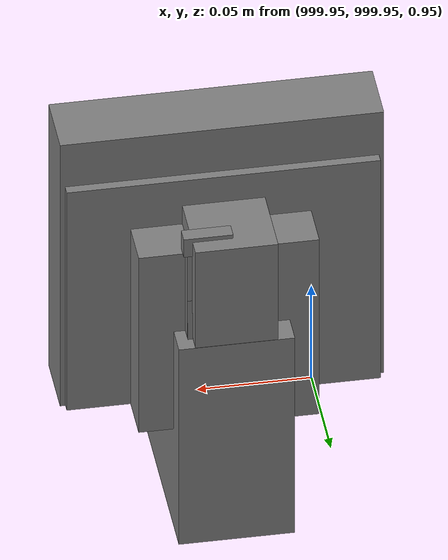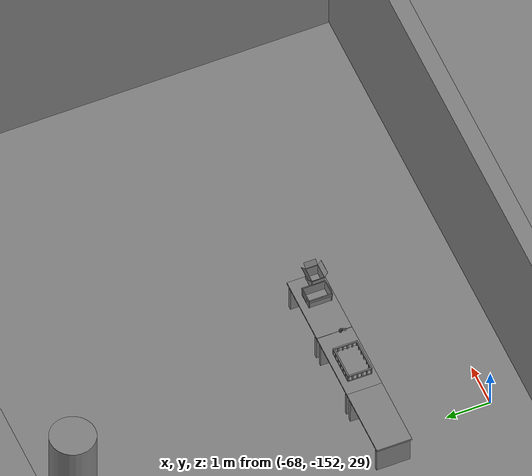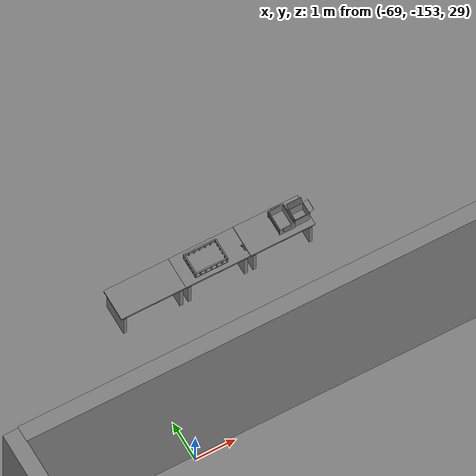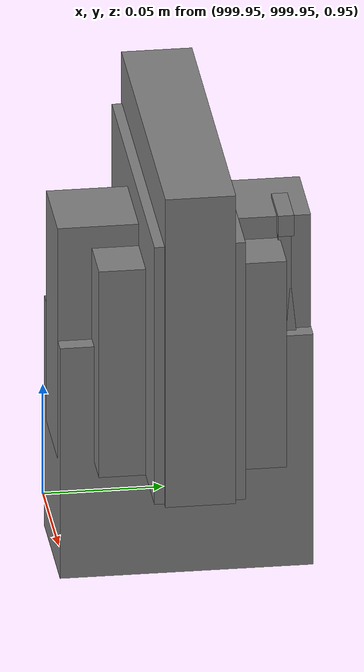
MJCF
<mujoco>
    <option gravity="0.000000000 0.000000000 -9.810000420" timestep="0.0049999999" integrator="implicitfast" density="1.225" viscosity="1.8000001e-05" noslip_iterations="10" iterations="100" sdf_iterations="50">
        <flag multiccd="disable"/>
    </option>
    <size memory="1000M"/>
    <compiler coordinate="local"/>
    <worldbody>
        <light cutoff="30" pos="0 1 1" dir="0 -1 -2"/>
        <light cutoff="30" pos="0 -1 1" dir="0 1 -2"/>
        <body pos="1000.000000000 1000.000000000 1.000000000" euler="0.000000000 0.000000000 180.000000000" name="openloong_gripper_2f85_fix_base_usda_battery_01">
            <geom contype="1" conaffinity="1" density="1000" type="box" material="" rgba="0.500000000 0.500000000 0.500000000 1.000000000" solimp="0.899999976 0.949999988 0.001000000" friction="1.000000000 0.005000000 0.000100000" solref="0.020000000 1.000000000" margin="0" condim="3" group="0" pos="-0.011123657 -0.041940309 0.101691343" quat="1.000000000 0.000000000 0.000000000 0.000000000" size="0.010800000 0.003375000 0.004725000" name="openloong_gripper_2f85_fix_base_usda_geom_670CC48A_B559_4FEE_8E49_B8A96DBF579F"/>
            <geom contype="1" conaffinity="1" density="1000" type="box" material="" rgba="0.500000000 0.500000000 0.500000000 1.000000000" solimp="0.899999976 0.949999988 0.001000000" friction="1.000000000 0.005000000 0.000100000" solref="0.020000000 1.000000000" margin="0" condim="3" group="0" pos="-0.010876465 -0.044247437 0.047066893" quat="0.998702705 -0.050920475 0.000000000 0.000000000" size="0.009450001 0.002700000 0.024975000" name="openloong_gripper_2f85_fix_base_usda_geom_1890F4A7_38EE_40C9_B207_860A7B29A160"/>
            <geom contype="1" conaffinity="1" density="1000" type="box" material="" rgba="0.500000000 0.500000000 0.500000000 1.000000000" solimp="0.899999976 0.949999988 0.001000000" friction="1.000000000 0.005000000 0.000100000" solref="0.020000000 1.000000000" margin="0" condim="3" group="0" pos="-0.001235962 -0.000659180 0.047381196" quat="1.000000000 0.000000000 0.000000000 0.000000000" size="0.039420001 0.039150000 0.047250003" name="openloong_gripper_2f85_fix_base_usda_geom_7812D964_920F_49F6_BE12_A74B1D15FA24"/>
            <geom contype="1" conaffinity="1" density="1000" type="box" material="" rgba="0.500000000 0.500000000 0.500000000 1.000000000" solimp="0.899999976 0.949999988 0.001000000" friction="1.000000000 0.005000000 0.000100000" solref="0.020000000 1.000000000" margin="0" condim="3" group="0" pos="-0.010876465 -0.039138794 0.009851727" quat="1.000000000 0.000000000 0.000000000 0.000000000" size="0.009450001 0.010800000 0.013500000" name="openloong_gripper_2f85_fix_base_usda_geom_C46F956D_BC44_4AAB_8C7E_622E19574B89"/>
            <geom contype="1" conaffinity="1" density="1000" type="box" material="" rgba="0.500000000 0.500000000 0.500000000 1.000000000" solimp="0.899999976 0.949999988 0.001000000" friction="1.000000000 0.005000000 0.000100000" solref="0.020000000 1.000000000" margin="0" condim="3" group="0" pos="-0.010876465 -0.041528322 0.071508206" quat="1.000000000 0.000000000 0.000000000 0.000000000" size="0.009450001 0.002700000 0.027000001" name="openloong_gripper_2f85_fix_base_usda_geom_9EB8AA7A_B25D_442E_89A3_8ADD894BBA47"/>
            <freejoint name="openloong_gripper_2f85_fix_base_usda_battery_01_joint"/>
            <site size="0.005000000 0.005000000 0.005000000" rgba="0.500000000 0.500000000 0.500000000 1.000000000" pos="0.000000000 0.000000000 0.000000000" quat="0.999961913 0.008726500 0.000000000 0.000000000" group="0" type="sphere" name="openloong_gripper_2f85_fix_base_usda_battery_01site"/>
        </body>
        <body pos="-66.370918274 -149.622711182 31.162151337" euler="-171.031967163 84.872550964 100.962097168" mocap="true" name="spotlight6_SpotLight"/>
        <body pos="-65.986892700 -149.403869629 31.169969559" euler="-28.735023499 -17.143377304 -123.770591736" mocap="true" name="spotlight3_SpotLight"/>
        <body pos="1000.000000000 1000.000000000 1.000000000" euler="0.000000000 0.000000000 180.000000000" name="openloong_gripper_2f85_fix_base_usda_cpu_fan">
            <geom contype="1" conaffinity="1" density="1000" type="box" material="" rgba="0.500000000 0.500000000 0.500000000 1.000000000" solimp="0.899999976 0.949999988 0.001000000" friction="1.000000000 0.005000000 0.000100000" solref="0.020000000 1.000000000" margin="0" condim="3" group="0" pos="0.000000000 0.000000000 0.070034981" quat="0.000000000 0.000000000 0.000000000 1.000000000" size="0.070700005 0.014699999 0.070700005" name="openloong_gripper_2f85_fix_base_usda_geom_8635475A_8465_4872_8AAC_D612A11AA9C2"/>
            <freejoint name="openloong_gripper_2f85_fix_base_usda_cpu_fan_joint"/>
            <site size="0.005000000 0.005000000 0.005000000" rgba="0.500000000 0.500000000 0.500000000 1.000000000" pos="0.000000000 0.000000000 0.000000000" quat="0.999961913 0.008726535 0.000000000 0.000000000" group="0" type="sphere" name="openloong_gripper_2f85_fix_base_usda_cpu_fancsite"/>
        </body>
        <body pos="1000.000000000 1000.000000000 1.000000000" euler="0.000000000 0.000000000 180.000000000" name="openloong_gripper_2f85_fix_base_usda_wifi_box">
            <geom contype="1" conaffinity="1" density="1000" type="box" material="" rgba="0.500000000 0.500000000 0.500000000 1.000000000" solimp="0.899999976 0.949999988 0.001000000" friction="1.000000000 0.005000000 0.000100000" solref="0.020000000 1.000000000" margin="0" condim="3" group="0" pos="0.000000000 0.000000000 0.058978677" quat="0.000000000 0.000000047 0.000000000 1.000000000" size="0.068499997 0.018999999 0.059000000" name="openloong_gripper_2f85_fix_base_usda_geom_3FD60F5B_C207_4D11_902C_475292C4F218"/>
            <freejoint name="openloong_gripper_2f85_fix_base_usda_wifi_box_joint"/>
            <site size="0.005000000 0.005000000 0.005000000" rgba="0.500000000 0.500000000 0.500000000 1.000000000" pos="0.000000000 0.000000000 0.000000000" quat="0.999961913 0.008726500 0.000000000 0.000000000" group="0" type="sphere" name="openloong_gripper_2f85_fix_base_usda_wifi_boxsite"/>
        </body>
        <body pos="1000.000000000 1000.000000000 1.000000000" euler="0.000011953 0.000005123 -179.999984741" name="openloong_gripper_2f85_fix_base_usda_intel_box">
            <geom contype="1" conaffinity="1" density="1000" type="box" material="" rgba="0.500000000 0.500000000 0.500000000 1.000000000" solimp="0.899999976 0.949999988 0.001000000" friction="1.000000000 0.005000000 0.000100000" solref="0.020000000 1.000000000" margin="0" condim="3" group="0" pos="0.000000000 -0.000067139 0.000082284" quat="0.707106709 0.000000225 0.000000253 0.707106650" size="0.052800003 0.025300000 0.052800003" name="openloong_gripper_2f85_fix_base_usda_geom_2ADC73C2_509C_4FDE_AA9E_FD21F156A550"/>
            <freejoint name="openloong_gripper_2f85_fix_base_usda_intel_box_joint"/>
            <site size="0.005000000 0.005000000 0.005000000" rgba="0.500000000 0.500000000 0.500000000 1.000000000" pos="0.000000000 0.000000000 0.000000000" quat="0.999961913 0.008726500 0.000000000 0.000000000" group="0" type="sphere" name="openloong_gripper_2f85_fix_base_usda_intel_boxsite"/>
        </body>
        <body pos="1000.000000000 999.999938965 1.000000000" euler="0.000000000 0.000000000 180.000000000" name="openloong_gripper_2f85_fix_base_usda_intelcore_i5">
            <geom contype="1" conaffinity="1" density="1000" type="box" material="" rgba="0.500000000 0.500000000 0.500000000 1.000000000" solimp="0.899999976 0.949999988 0.001000000" friction="1.000000000 0.005000000 0.000100000" solref="0.020000000 1.000000000" margin="0" condim="3" group="0" pos="0.000000000 0.000000000 0.051722717" quat="0.707106709 0.000000000 0.000000000 -0.707106769" size="0.052800000 0.018080002 0.052800000" name="openloong_gripper_2f85_fix_base_usda_geom_A4C3DC68_986D_4E59_B199_9ACA6E830BC7"/>
            <freejoint name="openloong_gripper_2f85_fix_base_usda_intelcore_i5_joint"/>
            <site size="0.005000000 0.005000000 0.005000000" rgba="0.500000000 0.500000000 0.500000000 1.000000000" pos="0.000000000 0.000000000 0.000000000" quat="0.999961913 0.008726534 0.000000000 0.000000000" group="0" type="sphere" name="openloong_gripper_2f85_fix_base_usda_intelcore_i5site"/>
        </body>
        <body pos="-65.970031738 -149.738571167 31.171194077" euler="-63.414485931 47.621250153 -107.802482605" mocap="true" name="spotlight2_SpotLight"/>
        <body pos="-64.866622925 -149.383972168 30.183746338" euler="89.999984741 89.999946594 0.000000000" name="openloong_gripper_2f85_fix_base_usda_bluebox_01">
            <geom contype="1" conaffinity="1" density="1000" type="box" material="" rgba="0.500000000 0.500000000 0.500000000 1.000000000" solimp="0.899999976 0.949999988 0.001000000" friction="1.000000000 0.005000000 0.000100000" solref="0.020000000 1.000000000" margin="0" condim="3" group="0" pos="0.276580811 0.187225342 0.000068665" quat="0.707106948 0.000077471 0.707106352 0.000077486" size="0.100000001 0.057999998 0.010000000" name="openloong_gripper_2f85_fix_base_usda_geom_C6E534B7_5867_44EB_8AC1_54FDFBB9D792"/>
            <geom contype="1" conaffinity="1" density="1000" type="box" material="" rgba="0.500000000 0.500000000 0.500000000 1.000000000" solimp="0.899999976 0.949999988 0.001000000" friction="1.000000000 0.005000000 0.000100000" solref="0.020000000 1.000000000" margin="0" condim="3" group="0" pos="0.000000000 0.002883911 0.000000000" quat="0.999999881 0.000000000 0.000000000 0.000000000" size="0.254000008 0.003000000 0.172000006" name="openloong_gripper_2f85_fix_base_usda_geom_17088BCD_F959_4C13_9E3B_2381D256C5F8"/>
            <geom contype="1" conaffinity="1" density="1000" type="box" material="" rgba="0.500000000 0.500000000 0.500000000 1.000000000" solimp="0.899999976 0.949999988 0.001000000" friction="1.000000000 0.005000000 0.000100000" solref="0.020000000 1.000000000" margin="0" condim="3" group="0" pos="0.000000000 0.124874115 0.173484802" quat="0.999796331 0.020176515 -0.000000015 0.000000030" size="0.259999990 0.119999997 0.007000000" name="openloong_gripper_2f85_fix_base_usda_geom_5D58AFFA_6866_4086_99DC_2A940C30C6D7"/>
            <geom contype="1" conaffinity="1" density="1000" type="box" material="" rgba="0.500000000 0.500000000 0.500000000 1.000000000" solimp="0.899999976 0.949999988 0.001000000" friction="1.000000000 0.005000000 0.000100000" solref="0.020000000 1.000000000" margin="0" condim="3" group="0" pos="0.000000000 0.124874115 -0.173469543" quat="0.999796331 -0.020176545 -0.000000015 0.000000000" size="0.259999990 0.119999997 0.007000000" name="openloong_gripper_2f85_fix_base_usda_geom_047986CA_B759_440C_B4E3_02E54035EB23"/>
            <geom contype="1" conaffinity="1" density="1000" type="box" material="" rgba="0.500000000 0.500000000 0.500000000 1.000000000" solimp="0.899999976 0.949999988 0.001000000" friction="1.000000000 0.005000000 0.000100000" solref="0.020000000 1.000000000" margin="0" condim="3" group="0" pos="0.000000000 0.214008331 0.188980103" quat="0.999912977 0.013176724 0.000000015 0.000000000" size="0.259999990 0.029999999 0.012500000" name="openloong_gripper_2f85_fix_base_usda_geom_3A5113CD_0BA3_45F4_B8C0_EB2217BC80FC"/>
            <geom contype="1" conaffinity="1" density="1000" type="box" material="" rgba="0.500000000 0.500000000 0.500000000 1.000000000" solimp="0.899999976 0.949999988 0.001000000" friction="1.000000000 0.005000000 0.000100000" solref="0.020000000 1.000000000" margin="0" condim="3" group="0" pos="-0.258361816 0.125289917 0.001876831" quat="0.702796936 -0.020792112 0.710783124 0.020769298" size="0.189999998 0.119999997 0.009000000" name="openloong_gripper_2f85_fix_base_usda_geom_C39C265B_678B_4051_8B27_92CF5985B023"/>
            <geom contype="1" conaffinity="1" density="1000" type="box" material="" rgba="0.500000000 0.500000000 0.500000000 1.000000000" solimp="0.899999976 0.949999988 0.001000000" friction="1.000000000 0.005000000 0.000100000" solref="0.020000000 1.000000000" margin="0" condim="3" group="0" pos="0.000000000 0.214008331 -0.188980103" quat="0.999912977 -0.013176769 0.000000030 0.000000015" size="0.259999990 0.029999999 0.012500000" name="openloong_gripper_2f85_fix_base_usda_geom_62421019_F23A_42A0_9AA8_FB77C44AEC5A"/>
            <geom contype="1" conaffinity="1" density="1000" type="box" material="" rgba="0.500000000 0.500000000 0.500000000 1.000000000" solimp="0.899999976 0.949999988 0.001000000" friction="1.000000000 0.005000000 0.000100000" solref="0.020000000 1.000000000" margin="0" condim="3" group="0" pos="-0.276611328 0.187225342 0.000068665" quat="0.707106650 0.000077441 0.707106709 0.000077456" size="0.100000001 0.057999998 0.010000000" name="openloong_gripper_2f85_fix_base_usda_geom_A50402CD_1D1E_4969_8987_1EBB916A408D"/>
            <geom contype="1" conaffinity="1" density="1000" type="box" material="" rgba="0.500000000 0.500000000 0.500000000 1.000000000" solimp="0.899999976 0.949999988 0.001000000" friction="1.000000000 0.005000000 0.000100000" solref="0.020000000 1.000000000" margin="0" condim="3" group="0" pos="0.258331299 0.125289917 0.001876831" quat="0.702851415 0.018856421 0.710823774 -0.019329369" size="0.189999998 0.119999997 0.009000000" name="openloong_gripper_2f85_fix_base_usda_geom_E0693261_8648_46A1_88C4_2A8ED107AD0D"/>
            <freejoint name="openloong_gripper_2f85_fix_base_usda_bluebox_01_joint"/>
            <site size="0.005000000 0.005000000 0.005000000" rgba="0.500000000 0.500000000 0.500000000 1.000000000" pos="0.000000000 0.000000000 0.000000000" quat="0.999961913 0.008726534 0.000000000 0.000000000" group="0" type="sphere" name="openloong_gripper_2f85_fix_base_usda_bluebox_01site"/>
        </body>
        <body pos="-64.496299744 -149.491867065 30.235729218" euler="0.000000000 0.000000000 89.999946594" name="openloong_gripper_2f85_fix_base_usda_cardboardbox_01">
            <geom contype="1" conaffinity="1" density="1000" type="box" material="" rgba="0.500000000 0.500000000 0.500000000 1.000000000" solimp="0.899999976 0.949999988 0.001000000" friction="1.000000000 0.005000000 0.000100000" solref="0.020000000 1.000000000" margin="0" condim="3" group="0" pos="-0.003166199 -0.004086494 0.005052090" quat="1.000000000 0.000000000 0.000000000 0.000000000" size="0.142499998 0.177500010 0.005000000" name="openloong_gripper_2f85_fix_base_usda_geom_CF652B77_38B4_471C_B14A_EBCCAFB3B508"/>
            <geom contype="1" conaffinity="1" density="1000" type="box" material="" rgba="0.500000000 0.500000000 0.500000000 1.000000000" solimp="0.899999976 0.949999988 0.001000000" friction="1.000000000 0.005000000 0.000100000" solref="0.020000000 1.000000000" margin="0" condim="3" group="0" pos="-0.003166199 0.170316696 0.150570869" quat="1.000000000 0.000000000 0.000000000 0.000000000" size="0.142499998 0.005000000 0.149999991" name="openloong_gripper_2f85_fix_base_usda_geom_5A4D7861_686A_4717_8EC4_A8EFF53D4EA3"/>
            <geom contype="1" conaffinity="1" density="1000" type="box" material="" rgba="0.500000000 0.500000000 0.500000000 1.000000000" solimp="0.899999976 0.949999988 0.001000000" friction="1.000000000 0.005000000 0.000100000" solref="0.020000000 1.000000000" margin="0" condim="3" group="0" pos="-0.147399902 -0.005307198 0.150570869" quat="1.000000000 0.000000000 0.000000000 0.000000000" size="0.005000000 0.177500010 0.149999991" name="openloong_gripper_2f85_fix_base_usda_geom_5BC6D2B2_921F_4228_B465_EAEF1D6E635D"/>
            <geom contype="1" conaffinity="1" density="1000" type="box" material="" rgba="0.500000000 0.500000000 0.500000000 1.000000000" solimp="0.899999976 0.949999988 0.001000000" friction="1.000000000 0.005000000 0.000100000" solref="0.020000000 1.000000000" margin="0" condim="3" group="0" pos="0.140275955 -0.005307198 0.150570869" quat="1.000000000 0.000000000 0.000000000 0.000000000" size="0.005000000 0.177500010 0.149999991" name="openloong_gripper_2f85_fix_base_usda_geom_D82D0377_7F85_4EFD_B3CF_0D82686A0C39"/>
            <geom contype="1" conaffinity="1" density="1000" type="box" material="" rgba="0.500000000 0.500000000 0.500000000 1.000000000" solimp="0.899999976 0.949999988 0.001000000" friction="1.000000000 0.005000000 0.000100000" solref="0.020000000 1.000000000" margin="0" condim="3" group="0" pos="-0.003166199 -0.181550980 0.150570869" quat="1.000000000 0.000000000 0.000000000 0.000000000" size="0.142499998 0.005000000 0.149999991" name="openloong_gripper_2f85_fix_base_usda_geom_C5524CB6_98E9_4ECE_A7A5_5380021E3136"/>
            <freejoint name="openloong_gripper_2f85_fix_base_usda_cardboardbox_01_joint"/>
            <site size="0.005000000 0.005000000 0.005000000" rgba="0.500000000 0.500000000 0.500000000 1.000000000" pos="0.000000000 0.000000000 0.000000000" quat="0.999961913 0.008726535 0.000000000 0.000000000" group="0" type="sphere" name="openloong_gripper_2f85_fix_base_usda_site_BAA2A15E_CA3F_4B46_B395_B56C73B929F2"/>
            <body pos="0.139160156 -0.004048347 0.301930904" euler="-179.999954224 49.383502960 179.999954224" name="openloong_gripper_2f85_fix_base_usda_A1_006">
                <geom contype="1" conaffinity="1" density="1000" type="box" material="" rgba="0.500000000 0.500000000 0.500000000 1.000000000" solimp="0.899999976 0.949999988 0.001000000" friction="1.000000000 0.005000000 0.000100000" solref="0.020000000 1.000000000" margin="0" condim="3" group="0" pos="-0.071587563 0.000009537 0.001745224" quat="0.999999881 0.000000000 0.000000000 0.000000000" size="0.071249999 0.179999992 0.002500000" name="openloong_gripper_2f85_fix_base_usda_geom_5C2852C8_C019_4D8F_9402_7C755E59FF66"/>
                <joint armature="0" stiffness="0.07" damping="0.0099999998" axis="0.000000 1.000000 0.000000" type="hinge" name="openloong_gripper_2f85_fix_base_usda_A1_006"/>
            </body>
            <body pos="-0.145902634 -0.004086494 0.301938057" euler="-180.000000000 -60.000011444 -180.000000000" name="openloong_gripper_2f85_fix_base_usda_A2_006">
                <geom contype="1" conaffinity="1" density="1000" type="box" material="" rgba="0.500000000 0.500000000 0.500000000 1.000000000" solimp="0.899999976 0.949999988 0.001000000" friction="1.000000000 0.005000000 0.000100000" solref="0.020000000 1.000000000" margin="0" condim="3" group="0" pos="0.071268082 0.000009537 0.002717972" quat="0.000002921 0.000000000 -0.000000030 0.999999881" size="0.071249999 0.179999992 0.002500000" name="openloong_gripper_2f85_fix_base_usda_geom_99A8E3F6_A844_4709_A654_8D79D6C17C7F"/>
                <joint armature="0" stiffness="0.07" damping="0.0099999998" axis="0.000000 1.000000 0.000000" type="hinge" name="openloong_gripper_2f85_fix_base_usda_A2_006"/>
            </body>
            <body pos="-0.003385544 0.175991058 0.301930904" euler="-125.858116150 -0.000004561 0.000002331" name="openloong_gripper_2f85_fix_base_usda_B2_006">
                <geom contype="1" conaffinity="1" density="1000" type="box" material="" rgba="0.500000000 0.500000000 0.500000000 1.000000000" solimp="0.899999976 0.949999988 0.001000000" friction="1.000000000 0.005000000 0.000100000" solref="0.020000000 1.000000000" margin="0" condim="3" group="0" pos="0.000009537 -0.070939064 -0.002470016" quat="0.999614120 0.027776197 -0.000000015 0.000000030" size="0.137500003 0.064999998 0.005000000" name="openloong_gripper_2f85_fix_base_usda_geom_2F0463CA_E2E2_466A_8AA0_DE91F0946D55"/>
                <joint armature="0" stiffness="0.07" damping="0.0099999998" axis="1.000000 0.000000 0.000000" type="hinge" name="openloong_gripper_2f85_fix_base_usda_B2_006"/>
            </body>
            <body pos="-0.003385544 -0.184140205 0.301938057" euler="147.805557251 0.000000000 0.000000000" name="openloong_gripper_2f85_fix_base_usda_B1_006">
                <geom contype="1" conaffinity="1" density="1000" type="box" material="" rgba="0.500000000 0.500000000 0.500000000 1.000000000" solimp="0.899999976 0.949999988 0.001000000" friction="1.000000000 0.005000000 0.000100000" solref="0.020000000 1.000000000" margin="0" condim="3" group="0" pos="-0.000028610 0.070202351 -0.002703667" quat="0.999614179 -0.027776167 0.000000000 0.000000000" size="0.137500003 0.064999998 0.005000000" name="openloong_gripper_2f85_fix_base_usda_geom_53C08A8D_6FDF_484A_BDFC_22CBEBCA4D4F"/>
                <joint armature="0" stiffness="0.07" damping="0.0099999998" axis="1.000000 0.000000 0.000000" type="hinge" name="openloong_gripper_2f85_fix_base_usda_B1_006"/>
            </body>
        </body>
        <body pos="-65.882858276 -149.481979370 30.229999542" euler="-64.487716675 0.000000000 0.000000000" name="openloong_gripper_2f85_fix_base_usda_Barcode">
            <geom contype="1" conaffinity="1" density="1000" type="box" material="" rgba="0.500000000 0.500000000 0.500000000 1.000000000" solimp="0.899999976 0.949999988 0.001000000" friction="1.000000000 0.005000000 0.000100000" solref="0.020000000 1.000000000" margin="0" condim="3" group="0" pos="0.000000000 0.013038635 0.001419067" quat="0.000000000 0.000000000 0.000000000 1.000000119" size="0.034000002 0.010000000 0.017999999" name="openloong_gripper_2f85_fix_base_usda_geom_2CBBB70A_EC09_4908_84B2_18C660FB56C9"/>
            <geom contype="1" conaffinity="1" density="1000" type="box" material="" rgba="0.500000000 0.500000000 0.500000000 1.000000000" solimp="0.899999976 0.949999988 0.001000000" friction="1.000000000 0.005000000 0.000100000" solref="0.020000000 1.000000000" margin="0" condim="3" group="0" pos="0.000000000 -0.035301208 -0.007095337" quat="0.000000000 0.000000000 -0.043619365 0.999048233" size="0.028999999 0.010000000 0.020000000" name="openloong_gripper_2f85_fix_base_usda_geom_3AB88931_D7F2_4C0B_8171_73C012FFF756"/>
            <geom contype="1" conaffinity="1" density="1000" type="box" material="" rgba="0.500000000 0.500000000 0.500000000 1.000000000" solimp="0.899999976 0.949999988 0.001000000" friction="1.000000000 0.005000000 0.000100000" solref="0.020000000 1.000000000" margin="0" condim="3" group="0" pos="0.000000000 -0.043411255 -0.011749268" quat="0.922262907 0.386563420 0.000000000 0.000000000" size="0.026000001 0.010000000 0.020000000" name="openloong_gripper_2f85_fix_base_usda_geom_D6B05A60_FE68_4930_981B_A53A5D47BADA"/>
            <geom contype="1" conaffinity="1" density="1000" type="box" material="" rgba="0.500000000 0.500000000 0.500000000 1.000000000" solimp="0.899999976 0.949999988 0.001000000" friction="1.000000000 0.005000000 0.000100000" solref="0.020000000 1.000000000" margin="0" condim="3" group="0" pos="0.000000000 -0.016967773 -0.031860352" quat="0.000000000 0.000000000 0.000000000 1.000000119" size="0.008000000 0.010000000 0.013000000" name="openloong_gripper_2f85_fix_base_usda_geom_503983DD_7134_48AE_85BF_95684FE35367"/>
            <geom contype="1" conaffinity="1" density="1000" type="box" material="" rgba="0.500000000 0.500000000 0.500000000 1.000000000" solimp="0.899999976 0.949999988 0.001000000" friction="1.000000000 0.005000000 0.000100000" solref="0.020000000 1.000000000" margin="0" condim="3" group="0" pos="0.000000000 -0.001869202 0.000312805" quat="0.953716993 0.300705761 0.000000000 0.000000000" size="0.032000002 0.010000000 0.018999999" name="openloong_gripper_2f85_fix_base_usda_geom_C88DE4D7_ADA7_41E9_8A9C_0150ACFE34D2"/>
            <geom contype="1" conaffinity="1" density="1000" type="box" material="" rgba="0.500000000 0.500000000 0.500000000 1.000000000" solimp="0.899999976 0.949999988 0.001000000" friction="1.000000000 0.005000000 0.000100000" solref="0.020000000 1.000000000" margin="0" condim="3" group="0" pos="0.000000000 -0.019531250 -0.003173828" quat="0.953716993 0.300705761 0.000000000 0.000000000" size="0.030999999 0.010000000 0.020000000" name="openloong_gripper_2f85_fix_base_usda_geom_43FDB0AA_C9CD_429E_92FC_003B2B50B8EC"/>
            <geom contype="1" conaffinity="1" density="1000" type="box" material="" rgba="0.500000000 0.500000000 0.500000000 1.000000000" solimp="0.899999976 0.949999988 0.001000000" friction="1.000000000 0.005000000 0.000100000" solref="0.020000000 1.000000000" margin="0" condim="3" group="0" pos="0.000000000 -0.035301208 -0.007095337" quat="0.953716993 0.300705761 0.000000000 0.000000000" size="0.028999999 0.010000000 0.020000000" name="openloong_gripper_2f85_fix_base_usda_geom_A9F042B0_EEFA_42E5_864E_289450F1BDFC"/>
            <geom contype="1" conaffinity="1" density="1000" type="box" material="" rgba="0.500000000 0.500000000 0.500000000 1.000000000" solimp="0.899999976 0.949999988 0.001000000" friction="1.000000000 0.005000000 0.000100000" solref="0.020000000 1.000000000" margin="0" condim="3" group="0" pos="0.000000000 -0.042617798 -0.071121216" quat="0.000000000 0.000000000 0.000000000 1.000000119" size="0.013000000 0.021000000 0.059999999" name="openloong_gripper_2f85_fix_base_usda_geom_42DD0974_FDE7_4D6B_96D7_E3E8FAB29181"/>
            <freejoint name="openloong_gripper_2f85_fix_base_usda_Barcode_joint"/>
            <site size="0.005000000 0.005000000 0.005000000" rgba="0.500000000 0.500000000 0.500000000 1.000000000" pos="0.000000000 0.000000000 0.000000000" quat="1.000000000 0.000000000 0.000000000 0.000000000" group="0" type="sphere" name="openloong_gripper_2f85_fix_base_usda_Barcode_site"/>
        </body>
        <body pos="-66.745018005 -149.392349243 30.184000015" euler="0.000000000 0.000000000 89.999946594" name="[22330737774960]_Basket_01">
            <geom contype="1" conaffinity="1" density="1000" type="box" material="" rgba="0.500000000 0.500000000 0.500000000 1.000000000" solimp="0.899999976 0.949999988 0.001000000" friction="1.000000000 0.005000000 0.000100000" solref="0.020000000 1.000000000" margin="0" condim="3" group="0" pos="-0.052425385 0.389207840 0.089787483" quat="0.707107008 0.000000000 0.000000000 0.707106411" size="0.014249999 0.014249999 0.059999999" name="[22330737774960]_geom_CD63DB8D_CC94_4D92_B1CC_61B971150A06"/>
            <geom contype="1" conaffinity="1" density="1000" type="box" material="" rgba="0.500000000 0.500000000 0.500000000 1.000000000" solimp="0.899999976 0.949999988 0.001000000" friction="1.000000000 0.005000000 0.000100000" solref="0.020000000 1.000000000" margin="0" condim="3" group="0" pos="0.264015198 -0.133043289 0.089787483" quat="0.707107008 0.000000000 0.000000000 0.707106411" size="0.014249999 0.014249999 0.059999999" name="[22330737774960]_geom_CDF0EE5A_4831_49AF_87FC_25BFCA85558B"/>
            <geom contype="1" conaffinity="1" density="1000" type="box" material="" rgba="0.500000000 0.500000000 0.500000000 1.000000000" solimp="0.899999976 0.949999988 0.001000000" friction="1.000000000 0.005000000 0.000100000" solref="0.020000000 1.000000000" margin="0" condim="3" group="0" pos="-0.264015198 -0.265548706 0.089793205" quat="0.707107008 0.000000000 0.000000000 0.707106411" size="0.014249999 0.014249999 0.059999999" name="[22330737774960]_geom_2A0E1777_1583_492A_B9B3_1C9E0D64559E"/>
            <geom contype="1" conaffinity="1" density="1000" type="box" material="" rgba="0.500000000 0.500000000 0.500000000 1.000000000" solimp="0.899999976 0.949999988 0.001000000" friction="1.000000000 0.005000000 0.000100000" solref="0.020000000 1.000000000" margin="0" condim="3" group="0" pos="-0.160263062 -0.389322281 0.089793205" quat="0.707107008 0.000000000 0.000000000 0.707106411" size="0.014249999 0.014249999 0.059999999" name="[22330737774960]_geom_5453D4CB_AF67_4A31_9B40_E8382F80420B"/>
            <geom contype="1" conaffinity="1" density="1000" type="box" material="" rgba="0.500000000 0.500000000 0.500000000 1.000000000" solimp="0.899999976 0.949999988 0.001000000" friction="1.000000000 0.005000000 0.000100000" solref="0.020000000 1.000000000" margin="0" condim="3" group="0" pos="0.162265778 -0.389322281 0.089787483" quat="0.707107008 0.000000000 0.000000000 0.707106411" size="0.014249999 0.014249999 0.059999999" name="[22330737774960]_geom_03E2E538_1C60_4582_A599_DF4C4CE3D72E"/>
            <geom contype="1" conaffinity="1" density="1000" type="box" material="" rgba="0.500000000 0.500000000 0.500000000 1.000000000" solimp="0.899999976 0.949999988 0.001000000" friction="1.000000000 0.005000000 0.000100000" solref="0.020000000 1.000000000" margin="0" condim="3" group="0" pos="0.264015198 0.389207840 0.089787483" quat="0.707107008 0.000000000 0.000000000 0.707106411" size="0.014249999 0.014249999 0.059999999" name="[22330737774960]_geom_DC2CDBAC_7D33_4A0D_A6CB_83F6175E330D"/>
            <geom contype="1" conaffinity="1" density="1000" type="box" material="" rgba="0.500000000 0.500000000 0.500000000 1.000000000" solimp="0.899999976 0.949999988 0.001000000" friction="1.000000000 0.005000000 0.000100000" solref="0.020000000 1.000000000" margin="0" condim="3" group="0" pos="-0.264015198 -0.133043289 0.089793205" quat="0.707107008 0.000000000 0.000000000 0.707106411" size="0.014249999 0.014249999 0.059999999" name="[22330737774960]_geom_1C4EC9D4_E66B_4461_9F30_F9005AF50EB7"/>
            <geom contype="1" conaffinity="1" density="1000" type="box" material="" rgba="0.500000000 0.500000000 0.500000000 1.000000000" solimp="0.899999976 0.949999988 0.001000000" friction="1.000000000 0.005000000 0.000100000" solref="0.020000000 1.000000000" margin="0" condim="3" group="0" pos="-0.264026642 0.269256592 0.089793205" quat="0.707107008 0.000000000 0.000000000 0.707106411" size="0.014249999 0.014249999 0.059999999" name="[22330737774960]_geom_DC1BAA39_ED2D_4C62_B747_852222FC53C2"/>
            <geom contype="1" conaffinity="1" density="1000" type="box" material="" rgba="0.500000000 0.500000000 0.500000000 1.000000000" solimp="0.899999976 0.949999988 0.001000000" friction="1.000000000 0.005000000 0.000100000" solref="0.020000000 1.000000000" margin="0" condim="3" group="0" pos="0.054462433 0.389207840 0.089787483" quat="0.707107008 0.000000000 0.000000000 0.707106411" size="0.014249999 0.014249999 0.059999999" name="[22330737774960]_geom_CE4534D8_AC6C_4471_952C_9FEF364CB32B"/>
            <geom contype="1" conaffinity="1" density="1000" type="box" material="" rgba="0.500000000 0.500000000 0.500000000 1.000000000" solimp="0.899999976 0.949999988 0.001000000" friction="1.000000000 0.005000000 0.000100000" solref="0.020000000 1.000000000" margin="0" condim="3" group="0" pos="0.054462433 -0.389322281 0.089787483" quat="0.707107008 0.000000000 0.000000000 0.707106411" size="0.014249999 0.014249999 0.059999999" name="[22330737774960]_geom_CA91AB92_FB8C_439F_A5C6_F26B7D874963"/>
            <geom contype="1" conaffinity="1" density="1000" type="box" material="" rgba="0.500000000 0.500000000 0.500000000 1.000000000" solimp="0.899999976 0.949999988 0.001000000" friction="1.000000000 0.005000000 0.000100000" solref="0.020000000 1.000000000" margin="0" condim="3" group="0" pos="0.264015198 0.269256592 0.089793205" quat="0.707107008 0.000000000 0.000000000 0.707106411" size="0.014249999 0.014249999 0.059999999" name="[22330737774960]_geom_737F4474_35F0_4DA7_92A1_68DBCFF3A1A7"/>
            <geom contype="1" conaffinity="1" density="1000" type="box" material="" rgba="0.500000000 0.500000000 0.500000000 1.000000000" solimp="0.899999976 0.949999988 0.001000000" friction="1.000000000 0.005000000 0.000100000" solref="0.020000000 1.000000000" margin="0" condim="3" group="0" pos="0.264015198 -0.389322281 0.089787483" quat="0.707107008 0.000000000 0.000000000 0.707106411" size="0.014249999 0.014249999 0.059999999" name="[22330737774960]_geom_582692F0_0225_407E_8284_54AEB450F241"/>
            <geom contype="1" conaffinity="1" density="1000" type="box" material="" rgba="0.500000000 0.500000000 0.500000000 1.000000000" solimp="0.899999976 0.949999988 0.001000000" friction="1.000000000 0.005000000 0.000100000" solref="0.020000000 1.000000000" margin="0" condim="3" group="0" pos="0.000000000 0.000000000 0.015998840" quat="0.707107008 0.000000000 0.000000000 0.707106411" size="0.403499991 0.279000014 0.015750000" name="[22330737774960]_geom_93FA71DD_F3D5_4A06_B3D8_B0851A397DB1"/>
            <geom contype="1" conaffinity="1" density="1000" type="box" material="" rgba="0.500000000 0.500000000 0.500000000 1.000000000" solimp="0.899999976 0.949999988 0.001000000" friction="1.000000000 0.005000000 0.000100000" solref="0.020000000 1.000000000" margin="0" condim="3" group="0" pos="0.000000000 -0.389476776 0.163619041" quat="0.707107008 0.000000000 0.000000000 0.707106411" size="0.015000000 0.277500004 0.015750000" name="[22330737774960]_geom_7DCD0C29_9770_463C_A1D5_0E267E17F044"/>
            <geom contype="1" conaffinity="1" density="1000" type="box" material="" rgba="0.500000000 0.500000000 0.500000000 1.000000000" solimp="0.899999976 0.949999988 0.001000000" friction="1.000000000 0.005000000 0.000100000" solref="0.020000000 1.000000000" margin="0" condim="3" group="0" pos="0.162265778 0.389207840 0.089787483" quat="0.707107008 0.000000000 0.000000000 0.707106411" size="0.014249999 0.014249999 0.059999999" name="[22330737774960]_geom_D0E51959_127A_4536_B9A0_731D26771A3D"/>
            <geom contype="1" conaffinity="1" density="1000" type="box" material="" rgba="0.500000000 0.500000000 0.500000000 1.000000000" solimp="0.899999976 0.949999988 0.001000000" friction="1.000000000 0.005000000 0.000100000" solref="0.020000000 1.000000000" margin="0" condim="3" group="0" pos="0.000000000 0.389471054 0.163619041" quat="0.707107008 0.000000000 0.000000000 0.707106411" size="0.015000000 0.277500004 0.015750000" name="[22330737774960]_geom_F0DACFEE_D62B_4A3E_83E7_416824248FF3"/>
            <geom contype="1" conaffinity="1" density="1000" type="box" material="" rgba="0.500000000 0.500000000 0.500000000 1.000000000" solimp="0.899999976 0.949999988 0.001000000" friction="1.000000000 0.005000000 0.000100000" solref="0.020000000 1.000000000" margin="0" condim="3" group="0" pos="-0.263511658 0.000000000 0.163619041" quat="0.707107008 0.000000000 0.000000000 0.707106411" size="0.403499991 0.015000000 0.015750000" name="[22330737774960]_geom_290A7E9B_A6F1_4706_8857_A5EB61468A62"/>
            <geom contype="1" conaffinity="1" density="1000" type="box" material="" rgba="0.500000000 0.500000000 0.500000000 1.000000000" solimp="0.899999976 0.949999988 0.001000000" friction="1.000000000 0.005000000 0.000100000" solref="0.020000000 1.000000000" margin="0" condim="3" group="0" pos="-0.264015198 0.141334534 0.089793205" quat="0.707107008 0.000000000 0.000000000 0.707106411" size="0.014249999 0.014249999 0.059999999" name="[22330737774960]_geom_A14E4BF5_8B3B_40B5_8C51_CB3C4BAA5935"/>
            <geom contype="1" conaffinity="1" density="1000" type="box" material="" rgba="0.500000000 0.500000000 0.500000000 1.000000000" solimp="0.899999976 0.949999988 0.001000000" friction="1.000000000 0.005000000 0.000100000" solref="0.020000000 1.000000000" margin="0" condim="3" group="0" pos="0.264015198 -0.265548706 0.089787483" quat="0.707107008 0.000000000 0.000000000 0.707106411" size="0.014249999 0.014249999 0.059999999" name="[22330737774960]_geom_0DABD49F_506F_4DAD_98ED_658BDCBDEDD7"/>
            <geom contype="1" conaffinity="1" density="1000" type="box" material="" rgba="0.500000000 0.500000000 0.500000000 1.000000000" solimp="0.899999976 0.949999988 0.001000000" friction="1.000000000 0.005000000 0.000100000" solref="0.020000000 1.000000000" margin="0" condim="3" group="0" pos="-0.160263062 0.389207840 0.089787483" quat="0.707107008 0.000000000 0.000000000 0.707106411" size="0.014249999 0.014249999 0.059999999" name="[22330737774960]_geom_527FE9BE_F6F0_4495_A99E_0D3DD3D266B0"/>
            <geom contype="1" conaffinity="1" density="1000" type="box" material="" rgba="0.500000000 0.500000000 0.500000000 1.000000000" solimp="0.899999976 0.949999988 0.001000000" friction="1.000000000 0.005000000 0.000100000" solref="0.020000000 1.000000000" margin="0" condim="3" group="0" pos="-0.052425385 -0.389322281 0.089787483" quat="0.707107008 0.000000000 0.000000000 0.707106411" size="0.014249999 0.014249999 0.059999999" name="[22330737774960]_geom_F5B77442_A732_4F6C_A558_5BEDB792D76B"/>
            <geom contype="1" conaffinity="1" density="1000" type="box" material="" rgba="0.500000000 0.500000000 0.500000000 1.000000000" solimp="0.899999976 0.949999988 0.001000000" friction="1.000000000 0.005000000 0.000100000" solref="0.020000000 1.000000000" margin="0" condim="3" group="0" pos="-0.264026642 -0.389322281 0.089793205" quat="0.707107008 0.000000000 0.000000000 0.707106411" size="0.014249999 0.014249999 0.059999999" name="[22330737774960]_geom_61CE6938_61F5_42BE_AA01_6783B2B333E3"/>
            <geom contype="1" conaffinity="1" density="1000" type="box" material="" rgba="0.500000000 0.500000000 0.500000000 1.000000000" solimp="0.899999976 0.949999988 0.001000000" friction="1.000000000 0.005000000 0.000100000" solref="0.020000000 1.000000000" margin="0" condim="3" group="0" pos="0.264015198 0.141334534 0.089787483" quat="0.707107008 0.000000000 0.000000000 0.707106411" size="0.014249999 0.014249999 0.059999999" name="[22330737774960]_geom_D11BE980_68C5_4276_B13E_B26D6E593F7F"/>
            <geom contype="1" conaffinity="1" density="1000" type="box" material="" rgba="0.500000000 0.500000000 0.500000000 1.000000000" solimp="0.899999976 0.949999988 0.001000000" friction="1.000000000 0.005000000 0.000100000" solref="0.020000000 1.000000000" margin="0" condim="3" group="0" pos="-0.264015198 0.389207840 0.089793205" quat="0.707107008 0.000000000 0.000000000 0.707106411" size="0.014249999 0.014249999 0.059999999" name="[22330737774960]_geom_4A258EF4_3DDD_44D2_B62D_1CBFA186CCD9"/>
            <geom contype="1" conaffinity="1" density="1000" type="box" material="" rgba="0.500000000 0.500000000 0.500000000 1.000000000" solimp="0.899999976 0.949999988 0.001000000" friction="1.000000000 0.005000000 0.000100000" solref="0.020000000 1.000000000" margin="0" condim="3" group="0" pos="0.264015198 0.004480362 0.089787483" quat="0.707107008 0.000000000 0.000000000 0.707106411" size="0.014249999 0.014249999 0.059999999" name="[22330737774960]_geom_CC36D4A1_308B_4965_B3E7_4A780E6F0353"/>
            <geom contype="1" conaffinity="1" density="1000" type="box" material="" rgba="0.500000000 0.500000000 0.500000000 1.000000000" solimp="0.899999976 0.949999988 0.001000000" friction="1.000000000 0.005000000 0.000100000" solref="0.020000000 1.000000000" margin="0" condim="3" group="0" pos="0.263694763 -0.000011444 0.163619041" quat="0.707107008 0.000000000 0.000000000 0.707106411" size="0.403499991 0.015000000 0.015750000" name="[22330737774960]_geom_C226A316_EC15_4983_B923_E15AE55AB3AF"/>
            <geom contype="1" conaffinity="1" density="1000" type="box" material="" rgba="0.500000000 0.500000000 0.500000000 1.000000000" solimp="0.899999976 0.949999988 0.001000000" friction="1.000000000 0.005000000 0.000100000" solref="0.020000000 1.000000000" margin="0" condim="3" group="0" pos="-0.264015198 0.004480362 0.089793205" quat="0.707107008 0.000000000 0.000000000 0.707106411" size="0.014249999 0.014249999 0.059999999" name="[22330737774960]_geom_1DCB20CA_4E08_4FA8_8E78_550E5B1AC0B2"/>
            <freejoint name="[22330737774960]_joint_56EE6B8A_E5B7_4A87_9CE3_05DD29B1C6AE"/>
        </body>
        <body pos="0.000000000 0.000000000 0.000000000" euler="0.000000000 0.000000000 0.000000000" name="Static Objects_Static Objects">
            <geom contype="1" conaffinity="1" density="1000" type="box" material="" rgba="0.500000000 0.500000000 0.500000000 1.000000000" solimp="0.899999976 0.949999988 0.001000000" friction="1.000000000 0.005000000 0.000100000" solref="0.020000000 1.000000000" margin="0" condim="3" group="0" pos="-67.544113159 -149.365814209 29.727830887" quat="0.500000417 0.499999970 0.499999553 0.499999970" size="0.381000012 0.319999993 0.041000001" name="Static Objects_geom_BD6C7CA2_1352_4507_BC5B_D362F3058626"/>
            <geom contype="1" conaffinity="1" density="1000" type="box" material="" rgba="0.500000000 0.500000000 0.500000000 1.000000000" solimp="0.899999976 0.949999988 0.001000000" friction="1.000000000 0.005000000 0.000100000" solref="0.020000000 1.000000000" margin="0" condim="3" group="0" pos="-68.239501953 -149.365814209 30.086868286" quat="0.500000417 0.499999970 0.499999553 0.499999970" size="0.370999992 0.039500002 0.745000005" name="Static Objects_geom_0A418ED0_FA44_4AA9_B2C2_67E4E6F0EDB6"/>
            <geom contype="1" conaffinity="1" density="1000" type="box" material="" rgba="0.500000000 0.500000000 0.500000000 1.000000000" solimp="0.899999976 0.949999988 0.001000000" friction="1.000000000 0.005000000 0.000100000" solref="0.020000000 1.000000000" margin="0" condim="3" group="0" pos="-68.239501953 -149.365814209 30.147235870" quat="0.500000417 0.499999970 0.499999553 0.499999970" size="0.400000006 0.022000000 0.800000012" name="Static Objects_geom_C452A85E_6DC8_42D7_89C5_795E03DE35C7"/>
            <geom contype="1" conaffinity="1" density="1000" type="box" material="" rgba="0.500000000 0.500000000 0.500000000 1.000000000" solimp="0.899999976 0.949999988 0.001000000" friction="1.000000000 0.005000000 0.000100000" solref="0.020000000 1.000000000" margin="0" condim="3" group="0" pos="-68.934890747 -149.365814209 29.727830887" quat="0.500000417 0.499999970 0.499999553 0.499999970" size="0.381000012 0.319999993 0.041000001" name="Static Objects_geom_BC38F7CC_1BB8_48C1_86BA_A30CAA4C8812"/>
            <geom contype="1" conaffinity="1" density="1000" type="box" material="" rgba="0.500000000 0.500000000 0.500000000 1.000000000" solimp="0.899999976 0.949999988 0.001000000" friction="1.000000000 0.005000000 0.000100000" solref="0.020000000 1.000000000" margin="0" condim="3" group="0" pos="-68.239501953 -149.365814209 29.561563492" quat="0.500000417 0.499999970 0.499999553 0.499999970" size="0.020000000 0.022000000 0.660000026" name="Static Objects_geom_7B9958BB_5672_4918_AF15_3560F6787CDE"/>
            <geom contype="1" conaffinity="1" density="1000" type="box" material="" rgba="0.500000000 0.500000000 0.500000000 1.000000000" solimp="0.899999976 0.949999988 0.001000000" friction="1.000000000 0.005000000 0.000100000" solref="0.020000000 1.000000000" margin="0" condim="3" group="0" pos="-65.945671082 -149.365814209 29.727830887" quat="0.500000417 0.499999970 0.499999553 0.499999970" size="0.381000012 0.319999993 0.041000001" name="Static Objects_geom_4F4C9F55_2E0F_4059_88F4_6BC760EB08DE"/>
            <geom contype="1" conaffinity="1" density="1000" type="box" material="" rgba="0.500000000 0.500000000 0.500000000 1.000000000" solimp="0.899999976 0.949999988 0.001000000" friction="1.000000000 0.005000000 0.000100000" solref="0.020000000 1.000000000" margin="0" condim="3" group="0" pos="-66.641059875 -149.365814209 30.086868286" quat="0.500000417 0.499999970 0.499999553 0.499999970" size="0.370999992 0.039500002 0.745000005" name="Static Objects_geom_20125215_D7DD_4FA0_9C7F_7ECBA8213C86"/>
            <geom contype="1" conaffinity="1" density="1000" type="box" material="" rgba="0.500000000 0.500000000 0.500000000 1.000000000" solimp="0.899999976 0.949999988 0.001000000" friction="1.000000000 0.005000000 0.000100000" solref="0.020000000 1.000000000" margin="0" condim="3" group="0" pos="-66.641059875 -149.365814209 30.147235870" quat="0.500000417 0.499999970 0.499999553 0.499999970" size="0.400000006 0.022000000 0.800000012" name="Static Objects_geom_E8B7EDC4_A676_4738_BA3E_35655E6C7079"/>
            <geom contype="1" conaffinity="1" density="1000" type="box" material="" rgba="0.500000000 0.500000000 0.500000000 1.000000000" solimp="0.899999976 0.949999988 0.001000000" friction="1.000000000 0.005000000 0.000100000" solref="0.020000000 1.000000000" margin="0" condim="3" group="0" pos="-67.336448669 -149.365814209 29.727830887" quat="0.500000417 0.499999970 0.499999553 0.499999970" size="0.381000012 0.319999993 0.041000001" name="Static Objects_geom_08E83ADF_8FEF_4D7B_8FEA_8C9985453B64"/>
            <geom contype="1" conaffinity="1" density="1000" type="box" material="" rgba="0.500000000 0.500000000 0.500000000 1.000000000" solimp="0.899999976 0.949999988 0.001000000" friction="1.000000000 0.005000000 0.000100000" solref="0.020000000 1.000000000" margin="0" condim="3" group="0" pos="-66.641059875 -149.365814209 29.561563492" quat="0.500000417 0.499999970 0.499999553 0.499999970" size="0.020000000 0.022000000 0.660000026" name="Static Objects_geom_C20D0D12_E90E_41A1_9AA7_9B2015471DAC"/>
            <geom contype="1" conaffinity="1" density="1000" type="box" material="" rgba="0.500000000 0.500000000 0.500000000 1.000000000" solimp="0.899999976 0.949999988 0.001000000" friction="1.000000000 0.005000000 0.000100000" solref="0.020000000 1.000000000" margin="0" condim="3" group="0" pos="-64.338577271 -149.365814209 29.727830887" quat="0.500000417 0.499999970 0.499999553 0.499999970" size="0.381000012 0.319999993 0.041000001" name="Static Objects_geom_F8D924BF_AA19_480B_B1E3_B2854B55EC36"/>
            <geom contype="1" conaffinity="1" density="1000" type="box" material="" rgba="0.500000000 0.500000000 0.500000000 1.000000000" solimp="0.899999976 0.949999988 0.001000000" friction="1.000000000 0.005000000 0.000100000" solref="0.020000000 1.000000000" margin="0" condim="3" group="0" pos="-65.033966064 -149.365814209 30.086868286" quat="0.500000417 0.499999970 0.499999553 0.499999970" size="0.370999992 0.039500002 0.745000005" name="Static Objects_geom_704D33E4_0B74_4B00_8B10_FC354885F83A"/>
            <geom contype="1" conaffinity="1" density="1000" type="box" material="" rgba="0.500000000 0.500000000 0.500000000 1.000000000" solimp="0.899999976 0.949999988 0.001000000" friction="1.000000000 0.005000000 0.000100000" solref="0.020000000 1.000000000" margin="0" condim="3" group="0" pos="-65.033966064 -149.365814209 30.147235870" quat="0.500000417 0.499999970 0.499999553 0.499999970" size="0.400000006 0.022000000 0.800000012" name="Static Objects_geom_B07B19ED_2C82_45D6_91A8_8E1F59D82909"/>
            <geom contype="1" conaffinity="1" density="1000" type="box" material="" rgba="0.500000000 0.500000000 0.500000000 1.000000000" solimp="0.899999976 0.949999988 0.001000000" friction="1.000000000 0.005000000 0.000100000" solref="0.020000000 1.000000000" margin="0" condim="3" group="0" pos="-65.729354858 -149.365814209 29.727830887" quat="0.500000417 0.499999970 0.499999553 0.499999970" size="0.381000012 0.319999993 0.041000001" name="Static Objects_geom_D6C370FD_FDDF_476E_A9FD_787E5D7EE032"/>
            <geom contype="1" conaffinity="1" density="1000" type="box" material="" rgba="0.500000000 0.500000000 0.500000000 1.000000000" solimp="0.899999976 0.949999988 0.001000000" friction="1.000000000 0.005000000 0.000100000" solref="0.020000000 1.000000000" margin="0" condim="3" group="0" pos="-65.033966064 -149.365814209 29.561563492" quat="0.500000417 0.499999970 0.499999553 0.499999970" size="0.020000000 0.022000000 0.660000026" name="Static Objects_geom_2ADF1E3B_09B6_4F40_8386_E3088A87C6E5"/>
            <geom contype="1" conaffinity="1" density="1000" type="box" material="" rgba="0.500000000 0.500000000 0.500000000 1.000000000" solimp="0.899999976 0.949999988 0.001000000" friction="1.000000000 0.005000000 0.000100000" solref="0.020000000 1.000000000" margin="0" condim="3" group="0" pos="-61.754566193 -137.853729248 33.906845093" quat="0.707107067 0.000000000 0.000000000 0.707106471" size="0.759999990 0.759999990 4.500000000" name="Static Objects_geom_5E417AF9_1671_40AD_8F1A_5E567187D9D8"/>
            <geom contype="1" conaffinity="1" density="1000" type="box" material="" rgba="0.500000000 0.500000000 0.500000000 1.000000000" solimp="0.899999976 0.949999988 0.001000000" friction="1.000000000 0.005000000 0.000100000" solref="0.020000000 1.000000000" margin="0" condim="3" group="0" pos="-57.511135101 -144.927108765 31.707921982" quat="1.000000000 0.000000000 0.000000000 0.000000000" size="0.200000003 8.000000000 2.299999952" name="Static Objects_geom_F13A8A11_E967_4294_88ED_2BD5E6305637"/>
            <geom contype="1" conaffinity="1" density="1000" type="box" material="" rgba="0.500000000 0.500000000 0.500000000 1.000000000" solimp="0.899999976 0.949999988 0.001000000" friction="1.000000000 0.005000000 0.000100000" solref="0.020000000 1.000000000" margin="0" condim="3" group="0" pos="-80.517646790 -157.574050903 31.688196182" quat="0.707107067 0.000000000 0.000000000 0.707106471" size="0.600000024 0.600000024 2.299999952" name="Static Objects_geom_FD6D85C2_C8A4_446D_B9A7_F9D52B13F92B"/>
            <geom contype="1" conaffinity="1" density="1000" type="box" material="" rgba="0.500000000 0.500000000 0.500000000 1.000000000" solimp="0.899999976 0.949999988 0.001000000" friction="1.000000000 0.005000000 0.000100000" solref="0.020000000 1.000000000" margin="0" condim="3" group="0" pos="-80.711044312 -147.414932251 31.666158676" quat="1.000000000 0.000000000 0.000000000 0.000000000" size="0.200000003 10.000000000 2.299999952" name="Static Objects_geom_11AFA74F_466E_4135_BFB3_F19FCBCCAF05"/>
            <geom contype="1" conaffinity="1" density="1000" type="box" material="" rgba="0.500000000 0.500000000 0.500000000 1.000000000" solimp="0.899999976 0.949999988 0.001000000" friction="1.000000000 0.005000000 0.000100000" solref="0.020000000 1.000000000" margin="0" condim="3" group="0" pos="-57.687217712 -137.434692383 31.688196182" quat="0.707107067 0.000000000 0.000000000 0.707106471" size="0.600000024 0.600000024 2.299999952" name="Static Objects_geom_3A93D6F5_10F3_4E86_915C_D35A20BC973F"/>
            <geom contype="1" conaffinity="1" density="1000" type="box" material="" rgba="0.500000000 0.500000000 0.500000000 1.000000000" solimp="0.899999976 0.949999988 0.001000000" friction="1.000000000 0.005000000 0.000100000" solref="0.020000000 1.000000000" margin="0" condim="3" group="0" pos="-69.537033081 -140.263229370 31.714921951" quat="0.707107067 0.000000000 0.000000000 0.707106471" size="0.759999990 4.500000000 2.299999952" name="Static Objects_geom_B94A9AEC_0530_4D11_93EE_5F7727CBC3B9"/>
            <geom contype="1" conaffinity="1" density="1000" type="box" material="" rgba="0.500000000 0.500000000 0.500000000 1.000000000" solimp="0.899999976 0.949999988 0.001000000" friction="1.000000000 0.005000000 0.000100000" solref="0.020000000 1.000000000" margin="0" condim="3" group="0" pos="-80.073638916 -137.853713989 33.906845093" quat="0.707107067 0.000000000 0.000000000 0.707106471" size="0.759999990 0.759999990 4.500000000" name="Static Objects_geom_77CF07A8_F1FB_4175_80CA_D87AF7A71B2C"/>
            <geom contype="1" conaffinity="1" density="1000" type="box" material="" rgba="0.500000000 0.500000000 0.500000000 1.000000000" solimp="0.899999976 0.949999988 0.001000000" friction="1.000000000 0.005000000 0.000100000" solref="0.020000000 1.000000000" margin="0" condim="3" group="0" pos="-73.406707764 -155.734664917 31.707921982" quat="1.000000000 0.000000000 0.000000000 0.000000000" size="0.200000003 3.000000000 2.299999952" name="Static Objects_geom_8134BEBA_5DF7_4959_9589_C99C577AFE62"/>
            <geom contype="1" conaffinity="1" density="1000" type="box" material="" rgba="0.500000000 0.500000000 0.500000000 1.000000000" solimp="0.899999976 0.949999988 0.001000000" friction="1.000000000 0.005000000 0.000100000" solref="0.020000000 1.000000000" margin="0" condim="3" group="0" pos="-68.497543335 -137.448257446 31.707921982" quat="0.707107067 0.000000000 0.000000000 0.707106471" size="0.200000003 14.000000000 2.299999952" name="Static Objects_geom_739120BF_D853_412E_B169_B2E13DFA0BFD"/>
            <geom contype="1" conaffinity="1" density="1000" type="cylinder" material="" rgba="0.500000000 0.500000000 0.500000000 1.000000000" solimp="0.899999976 0.949999988 0.001000000" friction="1.000000000 0.005000000 0.000100000" solref="0.020000000 1.000000000" margin="0" condim="3" group="0" pos="-68.868522644 -142.134506226 31.711090088" quat="0.707107067 0.000000000 0.000000000 0.707106471" size="0.509999990 2.299999952 1.000000000" name="Static Objects_geom_5E4CC5FE_2DEC_4C8D_9086_F21727CC765D"/>
            <geom contype="1" conaffinity="1" density="1000" type="plane" material="" rgba="0.500000000 0.500000000 0.500000000 1.000000000" solimp="0.899999976 0.949999988 0.001000000" friction="1.000000000 0.005000000 0.000100000" solref="0.020000000 1.000000000" margin="0" condim="3" group="0" pos="-72.873703003 -147.131927490 29.409669876" quat="1.000000000 0.000000000 0.000000000 0.000000000" size="18.000000000 14.000000000 1.000000000" name="Static Objects_geom_6C468698_2AC0_427E_AEC7_6947C29DC5D5"/>
            <geom contype="1" conaffinity="1" density="1000" type="box" material="" rgba="0.500000000 0.500000000 0.500000000 1.000000000" solimp="0.899999976 0.949999988 0.001000000" friction="1.000000000 0.005000000 0.000100000" solref="0.020000000 1.000000000" margin="0" condim="3" group="0" pos="-79.943580627 -157.782272339 31.707921982" quat="0.707107067 0.000000000 0.000000000 0.707106471" size="0.200000003 7.000000000 2.299999952" name="Static Objects_geom_0C042167_3279_4AAD_ABCF_B5D46AC53125"/>
            <geom contype="1" conaffinity="1" density="1000" type="box" material="" rgba="0.500000000 0.500000000 0.500000000 1.000000000" solimp="0.899999976 0.949999988 0.001000000" friction="1.000000000 0.005000000 0.000100000" solref="0.020000000 1.000000000" margin="0" condim="3" group="0" pos="-65.421028137 -152.903442383 31.707921982" quat="0.707107067 0.000000000 0.000000000 0.707106471" size="0.200000003 7.800000191 2.299999952" name="Static Objects_geom_E5F38C1A_897C_481E_9FFD_27CA75808908"/>
            <geom contype="1" conaffinity="1" density="1000" type="box" material="" rgba="0.500000000 0.500000000 0.500000000 1.000000000" solimp="0.899999976 0.949999988 0.001000000" friction="1.000000000 0.005000000 0.000100000" solref="0.020000000 1.000000000" margin="0" condim="3" group="0" pos="-74.776908875 -149.964416504 31.688196182" quat="1.000000000 0.000000000 0.000000000 0.000000000" size="0.600000024 0.409999996 2.299999952" name="Static Objects_geom_AFF67EC2_95F6_491A_AEDB_A7C605755F43"/>
            <geom contype="1" conaffinity="1" density="1000" type="cylinder" material="" rgba="0.500000000 0.500000000 0.500000000 1.000000000" solimp="0.899999976 0.949999988 0.001000000" friction="1.000000000 0.005000000 0.000100000" solref="0.020000000 1.000000000" margin="0" condim="3" group="0" pos="-60.161884308 -142.134506226 31.711090088" quat="0.707107067 0.000000000 0.000000000 0.707106471" size="0.509999990 2.299999952 1.000000000" name="Static Objects_geom_9B25BD35_4B02_406C_A07E_271919F7A649"/>
            <geom contype="1" conaffinity="1" density="1000" type="cylinder" material="" rgba="0.500000000 0.500000000 0.500000000 1.000000000" solimp="0.899999976 0.949999988 0.001000000" friction="1.000000000 0.005000000 0.000100000" solref="0.020000000 1.000000000" margin="0" condim="3" group="0" pos="-75.382453918 -149.963455200 31.711090088" quat="0.707107067 0.000000000 0.000000000 0.707106471" size="0.409999996 2.299999952 1.000000000" name="Static Objects_geom_B524EAE4_7715_455D_9BF9_AC3BCEA33B0F"/>
            <geom contype="1" conaffinity="1" density="1000" type="cylinder" material="" rgba="0.500000000 0.500000000 0.500000000 1.000000000" solimp="0.899999976 0.949999988 0.001000000" friction="1.000000000 0.005000000 0.000100000" solref="0.020000000 1.000000000" margin="0" condim="3" group="0" pos="-74.154960632 -149.963455200 31.711090088" quat="0.707107067 0.000000000 0.000000000 0.707106471" size="0.409999996 2.299999952 1.000000000" name="Static Objects_geom_8DE3BD12_3E7C_4391_A375_A81ADE96F9AD"/>
            <geom contype="1" conaffinity="1" density="1000" type="cylinder" material="" rgba="0.500000000 0.500000000 0.500000000 1.000000000" solimp="0.899999976 0.949999988 0.001000000" friction="1.000000000 0.005000000 0.000100000" solref="0.020000000 1.000000000" margin="0" condim="3" group="0" pos="-77.566612244 -142.134506226 31.711090088" quat="0.707107067 0.000000000 0.000000000 0.707106471" size="0.509999990 2.299999952 1.000000000" name="Static Objects_geom_A1DFF3FF_E9FC_471B_97F4_16D122EA0592"/>
        </body>
        <body pos="-66.291030884 -149.869689941 29.018842697" euler="0.000000000 0.000000000 89.999946594" mocap="true" name="openloong_gripper_2f85_fix_base_usda_leftHandMocap"/>
        <body pos="-66.291030884 -149.869689941 29.018842697" euler="0.000000000 0.000000000 89.999946594" mocap="true" name="openloong_gripper_2f85_fix_base_usda_rightHandMocap"/>
        <body pos="-66.291030884 -149.869689941 30.218843460" euler="0.000000000 0.000000000 89.999946594" name="openloong_gripper_2f85_fix_base_usda_base_link">
            <geom contype="1" conaffinity="1" density="1000" type="mesh" material="" rgba="0.783999979 0.783999979 0.783999979 1.000000000" solimp="0.899999976 0.949999988 0.001000000" friction="1.000000000 0.005000000 0.000100000" solref="0.020000000 1.000000000" margin="0" condim="3" group="3" mesh="base_link" pos="0.000000000 0.000000000 0.000000000" quat="1.000000000 0.000000000 0.000000000 0.000000000" size="1.000000000 1.000000000 1.000000000" name="openloong_gripper_2f85_fix_base_usda__geom_7_B8C3F299_F25D_477B_8B37_DD4022DE947A"/>
            <site size="0.005000000 0.005000000 0.005000000" rgba="0.500000000 0.500000000 0.500000000 1.000000000" pos="0.000000000 0.000000000 0.000000000" quat="1.000000000 0.000000000 0.000000000 0.000000000" group="0" type="sphere" name="openloong_gripper_2f85_fix_base_usda_imu"/>
            <inertial mass="22.447001" pos="-0.005664100 -0.001336700 0.238289997" diaginertia="0.374352545 0.277180195 0.220617250" quat="0.999247074 0.035235517 -0.015086859 0.006023135"/>
            <body pos="0.000000000 0.000000000 0.299997330" euler="0.000000000 0.000000000 0.000000000" name="openloong_gripper_2f85_fix_base_usda_dummy_body">
                <geom contype="1" conaffinity="1" density="1000" type="sphere" material="" rgba="0.783999979 0.783999979 0.783999979 1.000000000" solimp="0.899999976 0.949999988 0.001000000" friction="1.000000000 0.005000000 0.000100000" solref="0.020000000 1.000000000" margin="0" condim="3" group="3" pos="0.000000000 0.000000000 0.000000000" quat="1.000000000 0.000000000 0.000000000 0.000000000" size="0.010000000 0.000000000 0.000000000" name="openloong_gripper_2f85_fix_base_usda__geom_8_1AA0B16A_43C1_4D97_AB68_D783EDF2F19A"/>
                <joint armature="0.0099999998" stiffness="0" damping="0.1" axis="0.000000 0.000000 1.000000" type="hinge" name="openloong_gripper_2f85_fix_base_usda_dummy_joint"/>
                <site size="0.010000000 0.005000000 0.005000000" rgba="0.500000000 0.500000000 0.500000000 1.000000000" pos="0.000000000 0.000000000 0.000000000" quat="1.000000000 0.000000000 0.000000000 0.000000000" group="3" type="sphere" name="openloong_gripper_2f85_fix_base_usda_dummy_site"/>
            </body>
            <body pos="0.009002686 0.000000000 0.406400681" euler="0.000000000 0.000000000 0.000000000" name="openloong_gripper_2f85_fix_base_usda_Link_head_yaw">
                <geom contype="1" conaffinity="1" density="1000" type="mesh" material="" rgba="0.783999979 0.783999979 0.783999979 1.000000000" solimp="0.899999976 0.949999988 0.001000000" friction="1.000000000 0.005000000 0.000100000" solref="0.020000000 1.000000000" margin="0" condim="3" group="3" mesh="Link_head_yaw" pos="0.000000000 0.000000000 0.000000000" quat="1.000000000 0.000000000 0.000000000 0.000000000" size="1.000000000 1.000000000 1.000000000" name="openloong_gripper_2f85_fix_base_usda__geom_10_3229AC18_8135_4DF9_8F10_BE0D0654FA66"/>
                <inertial mass="0.84249002" pos="0.000000000 -0.002081400 0.044801001" diaginertia="0.000700588 0.000629000 0.000553812" quat="0.706933022 -0.015675601 0.015677100 0.706933022"/>
                <body pos="0.000000000 -0.034599304 0.048500061" euler="0.000000000 0.000000000 0.000000000" name="openloong_gripper_2f85_fix_base_usda_Link_head_pitch">
                    <geom contype="1" conaffinity="1" density="1000" type="mesh" material="" rgba="0.783999979 0.783999979 0.783999979 1.000000000" solimp="0.899999976 0.949999988 0.001000000" friction="1.000000000 0.005000000 0.000100000" solref="0.020000000 1.000000000" margin="0" condim="3" group="3" mesh="Link_head_pitch" pos="0.000000000 0.000000000 0.000000000" quat="1.000000000 0.000000000 0.000000000 0.000000000" size="1.000000000 1.000000000 1.000000000" name="openloong_gripper_2f85_fix_base_usda__geom_12_A55E2E48_CF33_4FDA_B5C3_DAE060FDE726"/>
                    <inertial mass="1.3943" pos="0.020569000 0.033004001 0.125000000" diaginertia="0.006381400 0.006289940 0.004481460" quat="0.973390222 0.008406822 0.228157058 0.019624906"/>
                    <body pos="0.000000000 0.029998779 0.000000000" euler="0.000000000 0.000000000 0.000000000" name="openloong_gripper_2f85_fix_base_usda_neck_center_body">
                        <site size="0.010000000 0.005000000 0.005000000" rgba="0.500000000 0.500000000 0.500000000 1.000000000" pos="0.000000000 0.000000000 0.000000000" quat="1.000000000 0.000000000 0.000000000 0.000000000" group="3" type="sphere" name="openloong_gripper_2f85_fix_base_usda_neck_center_site"/>
                        <body pos="0.020004272 0.000000000 0.149999619" euler="-0.000002229 39.998176575 -90.000205994" name="openloong_gripper_2f85_fix_base_usda_camera_head">
                            <site size="0.010000000 0.005000000 0.005000000" rgba="0.500000000 0.500000000 0.500000000 1.000000000" pos="0.000000000 0.000000000 0.000000000" quat="1.000000000 0.000000000 0.000000000 0.000000000" group="3" type="sphere" name="openloong_gripper_2f85_fix_base_usda_camera_head_site"/>
                        </body>
                    </body>
                </body>
            </body>
            <body pos="0.003997803 -0.161598206 0.392200470" euler="0.000000000 0.000000000 0.000000000" name="openloong_gripper_2f85_fix_base_usda_Link_arm_r_01">
                <geom contype="1" conaffinity="1" density="1000" type="mesh" material="" rgba="0.783999979 0.783999979 0.783999979 1.000000000" solimp="0.899999976 0.949999988 0.001000000" friction="1.000000000 0.005000000 0.000100000" solref="0.020000000 1.000000000" margin="0" condim="3" group="3" mesh="Link_arm_r_01" pos="0.000000000 0.000000000 0.000000000" quat="1.000000000 0.000000000 0.000000000 0.000000000" size="1.000000000 1.000000000 1.000000000" name="openloong_gripper_2f85_fix_base_usda__geom_14_06E973FE_FDC9_44A6_9839_B0AA0A16E54C"/>
                <joint armature="0.0099999998" stiffness="0" damping="1" axis="0.000000 -1.000000 0.000000" limited="true" range="-170.000015259 170.000015259" type="hinge" name="openloong_gripper_2f85_fix_base_usda_J_arm_r_01"/>
                <inertial mass="0.75641" pos="0.004494600 -0.038293999 -0.000001874" diaginertia="0.000842990 0.000803050 0.000587120" quat="-0.000163502 0.707098067 0.000812463 0.707115054"/>
                <body pos="-0.041992188 -0.041000366 0.000000000" euler="0.000000000 0.000000000 0.000000000" name="openloong_gripper_2f85_fix_base_usda_Link_arm_r_02">
                    <geom contype="1" conaffinity="1" density="1000" type="mesh" material="" rgba="0.783999979 0.783999979 0.783999979 1.000000000" solimp="0.899999976 0.949999988 0.001000000" friction="1.000000000 0.005000000 0.000100000" solref="0.020000000 1.000000000" margin="0" condim="3" group="3" mesh="Link_arm_r_02" pos="0.000000000 0.000000000 0.000000000" quat="1.000000000 0.000000000 0.000000000 0.000000000" size="1.000000000 1.000000000 1.000000000" name="openloong_gripper_2f85_fix_base_usda__geom_16_DA65CBD8_874F_4ACC_A723_C8B996260B26"/>
                    <joint armature="0.0099999998" stiffness="0" damping="1" axis="-1.000000 0.000000 0.000000" limited="true" range="-105.000244141 105.000244141" type="hinge" name="openloong_gripper_2f85_fix_base_usda_J_arm_r_02"/>
                    <inertial mass="0.98500001" pos="0.041999999 -0.067430697 0.000000000" diaginertia="0.002262690 0.001730990 0.001154020" quat="0.500000000 0.500000000 -0.500000000 0.500000000"/>
                    <body pos="0.041992188 -0.122596741 0.000000000" euler="0.000000000 0.000000000 0.000000000" name="openloong_gripper_2f85_fix_base_usda_Link_arm_r_03">
                        <geom contype="1" conaffinity="1" density="1000" type="mesh" material="" rgba="0.783999979 0.783999979 0.783999979 1.000000000" solimp="0.899999976 0.949999988 0.001000000" friction="1.000000000 0.005000000 0.000100000" solref="0.020000000 1.000000000" margin="0" condim="3" group="3" mesh="Link_arm_r_03" pos="0.000000000 0.000000000 0.000000000" quat="1.000000000 0.000000000 0.000000000 0.000000000" size="1.000000000 1.000000000 1.000000000" name="openloong_gripper_2f85_fix_base_usda__geom_18_D84D09F8_347C_41DF_B110_753831F9C9ED"/>
                        <joint armature="0.0099999998" stiffness="0" damping="1" axis="0.000000 -1.000000 0.000000" limited="true" range="-170.000015259 170.000015259" type="hinge" name="openloong_gripper_2f85_fix_base_usda_J_arm_r_03"/>
                        <inertial mass="0.95899999" pos="-0.001413580 -0.164663002 0.020757901" diaginertia="0.002101340 0.002064590 0.000754802" quat="0.560480952 0.454391927 -0.443732947 0.531497955"/>
                        <body pos="0.035293579 -0.177406311 0.023998260" euler="0.000000000 0.000000000 0.000000000" name="openloong_gripper_2f85_fix_base_usda_Link_arm_r_04">
                            <geom contype="1" conaffinity="1" density="1000" type="mesh" material="" rgba="0.783999979 0.783999979 0.783999979 1.000000000" solimp="0.899999976 0.949999988 0.001000000" friction="1.000000000 0.005000000 0.000100000" solref="0.020000000 1.000000000" margin="0" condim="3" group="3" mesh="Link_arm_r_04" pos="0.000000000 0.000000000 0.000000000" quat="1.000000000 0.000000000 0.000000000 0.000000000" size="1.000000000 1.000000000 1.000000000" name="openloong_gripper_2f85_fix_base_usda__geom_20_0A75417B_3C8A_4E1F_9B7E_32348D31F173"/>
                            <joint armature="0.0099999998" stiffness="0" damping="1" axis="-1.000000 0.000000 0.000000" limited="true" range="0.000000000 170.000015259" type="hinge" name="openloong_gripper_2f85_fix_base_usda_J_arm_r_04"/>
                            <inertial mass="0.60000002" pos="-0.038727000 -0.060766999 -0.021003000" diaginertia="0.001092610 0.000712422 0.000645102" quat="0.327701002 0.632602990 -0.467366993 0.523443997"/>
                            <body pos="-0.035293579 -0.103492737 -0.023998260" euler="0.000000000 0.000000000 0.000000000" name="openloong_gripper_2f85_fix_base_usda_Link_arm_r_05">
                                <geom contype="1" conaffinity="1" density="1000" type="mesh" material="" rgba="0.783999979 0.783999979 0.783999979 1.000000000" solimp="0.899999976 0.949999988 0.001000000" friction="1.000000000 0.005000000 0.000100000" solref="0.020000000 1.000000000" margin="0" condim="3" group="3" mesh="Link_arm_r_05" pos="0.000000000 0.000000000 0.000000000" quat="1.000000000 0.000000000 0.000000000 0.000000000" size="1.000000000 1.000000000 1.000000000" name="openloong_gripper_2f85_fix_base_usda__geom_22_DFAAC637_7E01_4CAC_ACCD_ED5FE89C7256"/>
                                <joint armature="0.0099999998" stiffness="0" damping="1" axis="0.000000 -1.000000 0.000000" limited="true" range="-170.000015259 170.000015259" type="hinge" name="openloong_gripper_2f85_fix_base_usda_J_arm_r_05"/>
                                <inertial mass="0.68976003" pos="0.000032712 -0.068658002 -0.000111780" diaginertia="0.002522510 0.002411100 0.000448695" quat="0.707660973 0.706543028 -0.002603360 0.002470550"/>
                                <body pos="-0.026489258 -0.196502686 0.000000000" euler="0.000000000 0.000000000 0.000000000" name="openloong_gripper_2f85_fix_base_usda_Link_arm_r_06">
                                    <geom contype="1" conaffinity="1" density="1000" type="mesh" material="" rgba="0.783999979 0.783999979 0.783999979 1.000000000" solimp="0.899999976 0.949999988 0.001000000" friction="1.000000000 0.005000000 0.000100000" solref="0.020000000 1.000000000" margin="0" condim="3" group="3" mesh="Link_arm_r_06" pos="0.000000000 0.000000000 0.000000000" quat="1.000000000 0.000000000 0.000000000 0.000000000" size="1.000000000 1.000000000 1.000000000" name="openloong_gripper_2f85_fix_base_usda__geom_24_37982C08_A4F9_4EF0_A324_64D4EEBFCF03"/>
                                    <joint armature="0.0099999998" stiffness="0" damping="1" axis="1.000000 0.000000 0.000000" limited="true" range="-105.000244141 105.000244141" type="hinge" name="openloong_gripper_2f85_fix_base_usda_J_arm_r_06"/>
                                    <inertial mass="0.28" pos="0.026078001 -0.000000896 0.001663700" diaginertia="0.000156930 0.000145601 0.000104979" quat="0.707080841 0.001851080 0.001883810 0.707127810"/>
                                    <body pos="0.026489258 0.000000000 0.031799316" euler="0.000000000 0.000000000 0.000000000" name="openloong_gripper_2f85_fix_base_usda_Link_arm_r_07">
                                        <geom contype="1" conaffinity="1" density="1000" type="mesh" material="" rgba="0.783999979 0.783999979 0.783999979 1.000000000" solimp="0.899999976 0.949999988 0.001000000" friction="1.000000000 0.005000000 0.000100000" solref="0.020000000 1.000000000" margin="0" condim="3" group="3" mesh="Link_arm_r_07" pos="0.000000000 0.000000000 0.000000000" quat="1.000000000 0.000000000 0.000000000 0.000000000" size="1.000000000 1.000000000 1.000000000" name="openloong_gripper_2f85_fix_base_usda__geom_26_07CF1EDE_D690_43AA_A235_6ECC87702C0C"/>
                                        <joint armature="0.0099999998" stiffness="0" damping="1" axis="0.000000 0.000000 1.000000" limited="true" range="-60.000133514 60.000133514" type="hinge" name="openloong_gripper_2f85_fix_base_usda_J_arm_r_07"/>
                                        <inertial mass="0.61353999" pos="-0.007859000 -0.158170000 -0.027736001" diaginertia="0.003037610 0.002570910 0.000729379" quat="0.427542925 0.443532884 -0.553093910 0.560867906"/>
                                        <body pos="0.000000000 0.286994934 -0.270000458" euler="150.000350952 -0.000001649 -0.000000442" name="openloong_gripper_2f85_fix_base_usda_camera_wrist_r">
                                            <site size="0.010000000 0.005000000 0.005000000" rgba="0.500000000 0.500000000 0.500000000 1.000000000" pos="0.000000000 0.000000000 0.000000000" quat="1.000000000 0.000000000 0.000000000 0.000000000" group="3" type="sphere" name="openloong_gripper_2f85_fix_base_usda_camera_wrist_r_site"/>
                                        </body>
                                        <body pos="0.000000000 -0.220008850 -0.033002853" euler="0.000000000 0.000000000 179.999969482" name="openloong_gripper_2f85_fix_base_usda_ee_center_body_r">
                                            <site size="0.010000000 0.005000000 0.005000000" rgba="0.500000000 0.500000000 0.500000000 1.000000000" pos="0.000000000 0.000000000 0.000000000" quat="1.000000000 0.000000000 0.000000000 0.000000000" group="3" type="sphere" name="openloong_gripper_2f85_fix_base_usda_ee_center_site_r"/>
                                        </body>
                                        <body pos="0.000000000 -0.066001892 -0.031000137" euler="89.999984741 0.000000000 180.000000000" name="openloong_gripper_2f85_fix_base_usda_zbr_base_link">
                                            <geom contype="1" conaffinity="1" density="1000" type="mesh" material="" rgba="0.783999979 0.783999979 0.783999979 1.000000000" solimp="0.899999976 0.949999988 0.001000000" friction="1.000000000 0.005000000 0.000100000" solref="0.020000000 1.000000000" margin="0" condim="3" group="3" mesh="base" pos="0.000000000 0.000003815 -0.000007629" quat="1.000000000 0.000000000 0.000000000 0.000000000" size="1.000000238 1.000000238 1.000000238" name="openloong_gripper_2f85_fix_base_usda__geom_30_8C3ABE94_B7D5_4A14_BFA7_BB8B891EAA1B"/>
                                            <inertial mass="0.77744102" pos="0.000000000 -0.000027039 0.035467502" diaginertia="0.000260285 0.000225381 0.000152708" quat="0.999998808 -0.001528488 0.000000000 0.000000000"/>
                                            <body pos="-0.030609138 0.004745484 0.065696731" euler="-89.999984741 -0.000000000 0.000000000" name="openloong_gripper_2f85_fix_base_usda_r_left_driver">
                                                <geom contype="1" conaffinity="1" density="1000" type="mesh" material="" rgba="0.783999979 0.783999979 0.783999979 1.000000000" solimp="0.899999976 0.949999988 0.001000000" friction="1.000000000 0.005000000 0.000100000" solref="0.020000000 1.000000000" margin="0" condim="3" group="3" mesh="driver" pos="0.030609138 0.054901138 -0.004699708" quat="0.707106829 0.707106709 0.000000000 -0.000000000" size="1.000000238 1.000000238 1.000000238" name="openloong_gripper_2f85_fix_base_usda__geom_32_C0F3F2DF_EB0C_4663_8618_EC911C797546"/>
                                                <joint armature="0.0049999999" stiffness="0" damping="0.1" axis="0.000000 0.000000 1.000000" limited="true" range="0.000000000 51.566200256" type="hinge" name="openloong_gripper_2f85_fix_base_usda_r_left_driver_joint"/>
                                                <inertial mass="0.0089956298" pos="0.000000000 0.017754700 0.001073140" diaginertia="0.000001724 0.000001609 0.000000322" quat="0.681301236 0.732003212 0.000000000 0.000000000"/>
                                                <body pos="-0.031402595 0.004524232 -0.010200503" euler="0.000000000 0.000000000 180.000000000" name="openloong_gripper_2f85_fix_base_usda_r_left_coupler">
                                                    <geom contype="1" conaffinity="1" density="1000" type="mesh" material="" rgba="0.783999979 0.783999979 0.783999979 1.000000000" solimp="0.899999976 0.949999988 0.001000000" friction="1.000000000 0.005000000 0.000100000" solref="0.020000000 1.000000000" margin="0" condim="3" group="3" mesh="coupler" pos="-0.062011734 -0.050354015 0.005500795" quat="0.707106829 -0.707106709 0.000000000 -0.000000000" size="1.000000238 1.000000238 1.000000238" name="openloong_gripper_2f85_fix_base_usda__geom_34_91767548_04DC_4C69_9348_1F59C2532081"/>
                                                    <inertial mass="0.0140974" pos="0.000000000 0.003012090 0.023217499" diaginertia="0.000004162 0.000003522 0.000000888" quat="0.705635548 -0.045590367 0.045590367 0.705635548"/>
                                                </body>
                                            </body>
                                            <body pos="-0.012695315 -0.012001040 0.072212234" euler="-89.999984741 -0.000000000 0.000000000" name="openloong_gripper_2f85_fix_base_usda_r_left_spring_link">
                                                <geom contype="1" conaffinity="1" density="1000" type="mesh" material="" rgba="0.783999979 0.783999979 0.783999979 1.000000000" solimp="0.899999976 0.949999988 0.001000000" friction="1.000000000 0.005000000 0.000100000" solref="0.020000000 1.000000000" margin="0" condim="3" group="3" mesh="spring_link" pos="0.012695315 0.061416641 0.012050631" quat="0.707106829 0.707106709 0.000000000 -0.000000000" size="1.000000238 1.000000238 1.000000238" name="openloong_gripper_2f85_fix_base_usda__geom_36_8D64AEE8_EACE_4720_B395_900F1971047F"/>
                                                <joint armature="0.001" stiffness="0.050000001" damping="0.00125" axis="0.000000 0.000000 1.000000" limited="true" range="-17.000000000 51.566200256" type="hinge" name="openloong_gripper_2f85_fix_base_usda_r_left_spring_link_joint"/>
                                                <inertial mass="0.0221642" pos="-0.000000009 0.018162400 0.021265799" diaginertia="0.000008969 0.000006717 0.000002639" quat="0.663403213 -0.244737089 0.244737089 0.663403213"/>
                                                <body pos="-0.038208015 -0.042503368 0.002950669" euler="180.000000000 0.000000000 -0.002185660" name="openloong_gripper_2f85_fix_base_usda_r_left_follower">
                                                    <geom contype="1" conaffinity="1" density="1000" type="mesh" material="" rgba="0.783999979 0.783999979 0.783999979 1.000000000" solimp="0.899999976 0.949999988 0.001000000" friction="1.000000000 0.005000000 0.000100000" solref="0.020000000 1.000000000" margin="0" condim="3" group="3" mesh="tongue" pos="0.050918590 -0.103920005 -0.009099962" quat="0.707106829 -0.707106709 0.000000030 0.000000030" size="1.000000238 1.000000238 1.000000238" name="openloong_gripper_2f85_fix_base_usda__geom_40_ACB7BA62_06D5_4AE3_A58A_429102D8550D"/>
                                                    <geom contype="1" conaffinity="1" density="1000" type="mesh" material="" rgba="0.783999979 0.783999979 0.783999979 1.000000000" solimp="0.899999976 0.949999988 0.001000000" friction="1.000000000 0.005000000 0.000100000" solref="0.020000000 1.000000000" margin="0" condim="3" group="3" mesh="follower" pos="0.050918590 -0.103920005 -0.009099962" quat="0.707106829 -0.707106709 0.000000030 0.000000030" size="1.000000238 1.000000238 1.000000238" name="openloong_gripper_2f85_fix_base_usda__geom_39_90D914E4_4614_4C3B_8846_511E3F2F5488"/>
                                                    <joint armature="0.001" stiffness="0" damping="0.1" axis="0.000000 0.000000 1.000000" limited="true" range="-49.999961853 51.566200256" type="hinge" name="openloong_gripper_2f85_fix_base_usda_r_left_follower"/>
                                                    <inertial mass="0.0125222" pos="0.000000000 -0.011046000 0.012478600" diaginertia="0.000002674 0.000002456 0.000000602" quat="0.986436546 0.164143041 0.000000000 0.000000000"/>
                                                    <body pos="-0.037765510 -0.103912376 -0.009099962" euler="-89.999984741 0.000000000 0.000004829" name="openloong_gripper_2f85_fix_base_usda_r_left_pad">
                                                        <geom contype="1" conaffinity="1" density="1000" type="box" material="" rgba="0.550000012 0.550000012 0.550000012 1.000000000" solimp="0.949999988 0.990000010 0.001000000" friction="0.699999988 0.005000000 0.000100000" solref="0.020000000 1.000000000" margin="0" condim="3" group="3" mass="1e-06" pos="0.043243419 0.000003815 0.119995147" quat="0.999999881 0.000000000 0.000000000 0.000000000" size="0.002000001 0.011000003 0.009375002" name="openloong_gripper_2f85_fix_base_usda_r_left_pad1_FB4C3336_5E81_4E9A_A94F_9228B0F77DAD"/>
                                                        <geom contype="1" conaffinity="1" density="1000" type="box" material="" rgba="0.449999988 0.449999988 0.449999988 1.000000000" solimp="0.949999988 0.990000010 0.001000000" friction="0.600000024 0.005000000 0.000100000" solref="0.020000000 1.000000000" margin="0" condim="3" group="3" mass="1e-06" pos="0.043243419 0.000003815 0.138748199" quat="0.999999881 0.000000000 0.000000000 0.000000000" size="0.002000001 0.011000003 0.009375002" name="openloong_gripper_2f85_fix_base_usda_r_left_pad2_B0CF37E3_2D2A_4CA3_BE4A_961C22FC543D"/>
                                                    </body>
                                                </body>
                                            </body>
                                            <body pos="0.030593880 -0.004753114 0.065696731" euler="89.999984741 0.000000000 180.000000000" name="openloong_gripper_2f85_fix_base_usda_r_right_driver">
                                                <geom contype="1" conaffinity="1" density="1000" type="mesh" material="" rgba="0.783999979 0.783999979 0.783999979 1.000000000" solimp="0.899999976 0.949999988 0.001000000" friction="1.000000000 0.005000000 0.000100000" solref="0.020000000 1.000000000" margin="0" condim="3" group="3" mesh="driver" pos="0.030593880 0.054901138 -0.004699708" quat="0.707106829 0.707106709 0.000000000 0.000000000" size="1.000000238 1.000000238 1.000000238" name="openloong_gripper_2f85_fix_base_usda__geom_42_971053B5_E1B0_47C8_BBA4_B486C65B1A6D"/>
                                                <joint armature="0.0049999999" stiffness="0" damping="0.1" axis="0.000000 0.000000 1.000000" limited="true" range="0.000000000 51.566200256" type="hinge" name="openloong_gripper_2f85_fix_base_usda_r_right_driver_joint"/>
                                                <inertial mass="0.0089956298" pos="0.000000000 0.017754700 0.001073140" diaginertia="0.000001724 0.000001609 0.000000322" quat="0.681301236 0.732003212 0.000000000 0.000000000"/>
                                                <body pos="-0.031417854 0.004531861 -0.010202411" euler="0.000000000 0.000000000 180.000000000" name="openloong_gripper_2f85_fix_base_usda_r_right_coupler">
                                                    <geom contype="1" conaffinity="1" density="1000" type="mesh" material="" rgba="0.783999979 0.783999979 0.783999979 1.000000000" solimp="0.899999976 0.949999988 0.001000000" friction="1.000000000 0.005000000 0.000100000" solref="0.020000000 1.000000000" margin="0" condim="3" group="3" mesh="coupler" pos="-0.062042251 -0.050376903 0.005500795" quat="0.707106829 -0.707106709 0.000000000 0.000000000" size="1.000000238 1.000000238 1.000000238" name="openloong_gripper_2f85_fix_base_usda__geom_44_11F6D075_5E13_4F9E_990C_C6EC701CA74A"/>
                                                    <inertial mass="0.0140974" pos="0.000000000 0.003012090 0.023217499" diaginertia="0.000004162 0.000003522 0.000000888" quat="0.705635548 -0.045590367 0.045590367 0.705635548"/>
                                                </body>
                                            </body>
                                            <body pos="0.012695315 0.011997226 0.072219864" euler="89.999984741 0.000000000 180.000000000" name="openloong_gripper_2f85_fix_base_usda_r_right_spring_link">
                                                <geom contype="1" conaffinity="1" density="1000" type="mesh" material="" rgba="0.783999979 0.783999979 0.783999979 1.000000000" solimp="0.899999976 0.949999988 0.001000000" friction="1.000000000 0.005000000 0.000100000" solref="0.020000000 1.000000000" margin="0" condim="3" group="3" mesh="spring_link" pos="0.012695315 0.061424270 0.012048724" quat="0.707106829 0.707106709 0.000000000 0.000000000" size="1.000000238 1.000000238 1.000000238" name="openloong_gripper_2f85_fix_base_usda__geom_46_435043EA_6524_4E68_94FF_E50704D31240"/>
                                                <joint armature="0.001" stiffness="0.050000001" damping="0.00125" axis="0.000000 0.000000 1.000000" limited="true" range="-17.000000000 51.566200256" type="hinge" name="openloong_gripper_2f85_fix_base_usda_r_right_spring_link_joint"/>
                                                <inertial mass="0.0221642" pos="-0.000000009 0.018162400 0.021265799" diaginertia="0.000008969 0.000006717 0.000002639" quat="0.663403213 -0.244737089 0.244737089 0.663403213"/>
                                                <body pos="-0.038208015 -0.042495739 0.002950669" euler="180.000000000 0.000000000 0.000000000" name="openloong_gripper_2f85_fix_base_usda_r_right_follower">
                                                    <geom contype="1" conaffinity="1" density="1000" type="mesh" material="" rgba="0.783999979 0.783999979 0.783999979 1.000000000" solimp="0.899999976 0.949999988 0.001000000" friction="1.000000000 0.005000000 0.000100000" solref="0.020000000 1.000000000" margin="0" condim="3" group="3" mesh="follower" pos="0.050888073 -0.103927635 -0.009099962" quat="0.707106829 -0.707106709 0.000000000 0.000000000" size="1.000000238 1.000000238 1.000000238" name="openloong_gripper_2f85_fix_base_usda__geom_50_041B4726_16D1_4274_A186_5E09F13A2F8A"/>
                                                    <geom contype="1" conaffinity="1" density="1000" type="mesh" material="" rgba="0.783999979 0.783999979 0.783999979 1.000000000" solimp="0.899999976 0.949999988 0.001000000" friction="1.000000000 0.005000000 0.000100000" solref="0.020000000 1.000000000" margin="0" condim="3" group="3" mesh="tongue" pos="0.050888073 -0.103927635 -0.009099962" quat="0.707106829 -0.707106709 0.000000000 0.000000000" size="1.000000238 1.000000238 1.000000238" name="openloong_gripper_2f85_fix_base_usda__geom_49_46B38964_16B2_4BA6_96E8_BBCCD0145FED"/>
                                                    <joint armature="0.001" stiffness="0" damping="0.1" axis="0.000000 0.000000 1.000000" limited="true" range="-49.999961853 51.566200256" type="hinge" name="openloong_gripper_2f85_fix_base_usda_r_right_follower_joint"/>
                                                    <inertial mass="0.0125222" pos="0.000000000 -0.011046000 0.012478600" diaginertia="0.000002674 0.000002456 0.000000602" quat="0.986436546 0.164143041 0.000000000 0.000000000"/>
                                                    <body pos="-0.037811287 -0.103927635 -0.009099962" euler="-89.999984741 0.000000000 0.000000000" name="openloong_gripper_2f85_fix_base_usda_r_right_pad">
                                                        <geom contype="1" conaffinity="1" density="1000" type="box" material="" rgba="0.449999988 0.449999988 0.449999988 1.000000000" solimp="0.949999988 0.990000010 0.001000000" friction="0.600000024 0.005000000 0.000100000" solref="0.020000000 1.000000000" margin="0" condim="3" group="3" mass="1e-06" pos="0.043258678 0.000000000 0.138748199" quat="1.000000000 0.000000000 0.000000000 0.000000000" size="0.002000001 0.011000003 0.009375002" name="openloong_gripper_2f85_fix_base_usda_r_right_pad2_8CFCDA04_EFC1_49D3_AAFE_9274DE7C5E3F"/>
                                                        <geom contype="1" conaffinity="1" density="1000" type="box" material="" rgba="0.550000012 0.550000012 0.550000012 1.000000000" solimp="0.949999988 0.990000010 0.001000000" friction="0.699999988 0.005000000 0.000100000" solref="0.020000000 1.000000000" margin="0" condim="3" group="3" mass="1e-06" pos="0.043258678 0.000003815 0.120002776" quat="1.000000000 0.000000000 0.000000000 0.000000000" size="0.002000001 0.011000003 0.009375002" name="openloong_gripper_2f85_fix_base_usda_r_right_pad1_79B9B035_C5CF_4764_8B10_DCF3F144AF7C"/>
                                                    </body>
                                                </body>
                                            </body>
                                        </body>
                                    </body>
                                </body>
                            </body>
                        </body>
                    </body>
                </body>
            </body>
            <body pos="0.003997803 0.161590576 0.392200470" euler="0.000000000 0.000000000 0.000000000" name="openloong_gripper_2f85_fix_base_usda_Link_arm_l_01">
                <geom contype="1" conaffinity="1" density="1000" type="mesh" material="" rgba="0.783999979 0.783999979 0.783999979 1.000000000" solimp="0.899999976 0.949999988 0.001000000" friction="1.000000000 0.005000000 0.000100000" solref="0.020000000 1.000000000" margin="0" condim="3" group="3" mesh="Link_arm_l_01" pos="0.000000000 0.000000000 0.000000000" quat="1.000000000 0.000000000 0.000000000 0.000000000" size="1.000000000 1.000000000 1.000000000" name="openloong_gripper_2f85_fix_base_usda__geom_52_1C4383DE_8B34_451E_9587_1996FDBEE505"/>
                <joint armature="0.0099999998" stiffness="0" damping="1" axis="0.000000 1.000000 0.000000" limited="true" range="-170.000015259 170.000015259" type="hinge" name="openloong_gripper_2f85_fix_base_usda_J_arm_l_01"/>
                <inertial mass="0.75640601" pos="-0.004494650 0.038294200 -0.000001874" diaginertia="0.000842986 0.000803053 0.000587115" quat="-0.000812496 0.707115054 0.000163424 0.707098067"/>
                <body pos="0.042007446 0.041000366 0.000000000" euler="0.000000000 0.000000000 0.000000000" name="openloong_gripper_2f85_fix_base_usda_Link_arm_l_02">
                    <geom contype="1" conaffinity="1" density="1000" type="mesh" material="" rgba="0.783999979 0.783999979 0.783999979 1.000000000" solimp="0.899999976 0.949999988 0.001000000" friction="1.000000000 0.005000000 0.000100000" solref="0.020000000 1.000000000" margin="0" condim="3" group="3" mesh="Link_arm_l_02" pos="0.000000000 0.000000000 0.000000000" quat="1.000000000 0.000000000 0.000000000 0.000000000" size="1.000000000 1.000000000 1.000000000" name="openloong_gripper_2f85_fix_base_usda__geom_54_386FDB54_E454_41F3_8907_2E3C9C1A9BC1"/>
                    <joint armature="0.0099999998" stiffness="0" damping="1" axis="-1.000000 0.000000 0.000000" limited="true" range="-105.000244141 105.000244141" type="hinge" name="openloong_gripper_2f85_fix_base_usda_J_arm_l_02"/>
                    <inertial mass="0.98500001" pos="-0.041999999 0.067430697 0.000000000" diaginertia="0.002262690 0.001730990 0.001154020" quat="0.500000000 0.500000000 -0.500000000 0.500000000"/>
                    <body pos="-0.042007446 0.122596741 0.000000000" euler="0.000000000 0.000000000 0.000000000" name="openloong_gripper_2f85_fix_base_usda_Link_arm_l_03">
                        <geom contype="1" conaffinity="1" density="1000" type="mesh" material="" rgba="0.783999979 0.783999979 0.783999979 1.000000000" solimp="0.899999976 0.949999988 0.001000000" friction="1.000000000 0.005000000 0.000100000" solref="0.020000000 1.000000000" margin="0" condim="3" group="3" mesh="Link_arm_l_03" pos="0.000000000 0.000000000 0.000000000" quat="1.000000000 0.000000000 0.000000000 0.000000000" size="1.000000000 1.000000000 1.000000000" name="openloong_gripper_2f85_fix_base_usda__geom_56_3AFE4273_FBA6_4DE2_AF96_0253672DAAA2"/>
                        <joint armature="0.0099999998" stiffness="0" damping="1" axis="0.000000 1.000000 0.000000" limited="true" range="-170.000015259 170.000015259" type="hinge" name="openloong_gripper_2f85_fix_base_usda_J_arm_l_03"/>
                        <inertial mass="0.95899999" pos="0.001413580 0.164663002 0.020757901" diaginertia="0.002101340 0.002064590 0.000754802" quat="0.443732947 0.531497955 -0.560480952 0.454391927"/>
                        <body pos="-0.035293579 0.177406311 0.023998260" euler="0.000000000 0.000000000 0.000000000" name="openloong_gripper_2f85_fix_base_usda_Link_arm_l_04">
                            <geom contype="1" conaffinity="1" density="1000" type="mesh" material="" rgba="0.783999979 0.783999979 0.783999979 1.000000000" solimp="0.899999976 0.949999988 0.001000000" friction="1.000000000 0.005000000 0.000100000" solref="0.020000000 1.000000000" margin="0" condim="3" group="3" mesh="Link_arm_l_04" pos="0.000000000 0.000000000 0.000000000" quat="1.000000000 0.000000000 0.000000000 0.000000000" size="1.000000000 1.000000000 1.000000000" name="openloong_gripper_2f85_fix_base_usda__geom_58_DC86FD0F_BB78_456D_BFB7_815E92CD33BE"/>
                            <joint armature="0.0099999998" stiffness="0" damping="1" axis="1.000000 0.000000 0.000000" limited="true" range="0.000000000 170.000015259" type="hinge" name="openloong_gripper_2f85_fix_base_usda_J_arm_l_04"/>
                            <inertial mass="0.60000002" pos="0.038727000 0.060767200 -0.021003200" diaginertia="0.001092570 0.000712419 0.000645098" quat="0.467370987 0.523440003 -0.327692002 0.632607996"/>
                            <body pos="0.035293579 0.103500366 -0.023998260" euler="0.000000000 0.000000000 0.000000000" name="openloong_gripper_2f85_fix_base_usda_Link_arm_l_05">
                                <geom contype="1" conaffinity="1" density="1000" type="mesh" material="" rgba="0.783999979 0.783999979 0.783999979 1.000000000" solimp="0.899999976 0.949999988 0.001000000" friction="1.000000000 0.005000000 0.000100000" solref="0.020000000 1.000000000" margin="0" condim="3" group="3" mesh="Link_arm_l_05" pos="0.000000000 0.000000000 0.000000000" quat="1.000000000 0.000000000 0.000000000 0.000000000" size="1.000000000 1.000000000 1.000000000" name="openloong_gripper_2f85_fix_base_usda__geom_60_C6D9D7D6_FCE9_4A8D_BB24_C87D3DFD2EA5"/>
                                <joint armature="0.0099999998" stiffness="0" damping="1" axis="0.000000 1.000000 0.000000" limited="true" range="-170.000015259 170.000015259" type="hinge" name="openloong_gripper_2f85_fix_base_usda_J_arm_l_05"/>
                                <inertial mass="0.68976003" pos="-0.000032712 0.068658002 -0.000111780" diaginertia="0.002522510 0.002411100 0.000448695" quat="0.706543028 0.707660973 0.002470550 -0.002603360"/>
                                <body pos="0.026504517 0.196495056 0.000000000" euler="0.000000000 0.000000000 0.000000000" name="openloong_gripper_2f85_fix_base_usda_Link_arm_l_06">
                                    <geom contype="1" conaffinity="1" density="1000" type="mesh" material="" rgba="0.783999979 0.783999979 0.783999979 1.000000000" solimp="0.899999976 0.949999988 0.001000000" friction="1.000000000 0.005000000 0.000100000" solref="0.020000000 1.000000000" margin="0" condim="3" group="3" mesh="Link_arm_l_06" pos="0.000000000 0.000000000 0.000000000" quat="1.000000000 0.000000000 0.000000000 0.000000000" size="1.000000000 1.000000000 1.000000000" name="openloong_gripper_2f85_fix_base_usda__geom_62_73B7BF65_791D_448E_8E7F_2A9ECB3C28AB"/>
                                    <joint armature="0.0099999998" stiffness="0" damping="1" axis="-1.000000 0.000000 0.000000" limited="true" range="-105.000244141 105.000244141" type="hinge" name="openloong_gripper_2f85_fix_base_usda_J_arm_l_06"/>
                                    <inertial mass="0.28" pos="-0.026077701 0.000000896 0.001663730" diaginertia="0.000156927 0.000145598 0.000104981" quat="0.707080841 -0.001851280 -0.001884020 0.707127810"/>
                                    <body pos="-0.026504517 0.000000000 0.031799316" euler="0.000000000 0.000000000 0.000000000" name="openloong_gripper_2f85_fix_base_usda_Link_arm_l_07">
                                        <geom contype="1" conaffinity="1" density="1000" type="mesh" material="" rgba="0.783999979 0.783999979 0.783999979 1.000000000" solimp="0.899999976 0.949999988 0.001000000" friction="1.000000000 0.005000000 0.000100000" solref="0.020000000 1.000000000" margin="0" condim="3" group="3" mesh="Link_arm_l_07" pos="0.000000000 0.000000000 0.000000000" quat="1.000000000 0.000000000 0.000000000 0.000000000" size="1.000000000 1.000000000 1.000000000" name="openloong_gripper_2f85_fix_base_usda__geom_64_A58C8D31_B826_4D08_B9E8_69ECB3782C66"/>
                                        <joint armature="0.0099999998" stiffness="0" damping="1" axis="0.000000 0.000000 1.000000" limited="true" range="-60.000133514 60.000133514" type="hinge" name="openloong_gripper_2f85_fix_base_usda_J_arm_l_07"/>
                                        <inertial mass="0.61353999" pos="-0.007787200 0.157049999 -0.027733000" diaginertia="0.003037200 0.002570420 0.000729374" quat="0.443562120 0.427539080 -0.560871124 0.553070128"/>
                                        <body pos="0.000000000 -0.286994934 -0.270000458" euler="-150.000350952 0.000001955 179.976669312" name="openloong_gripper_2f85_fix_base_usda_camera_wrist_l">
                                            <site size="0.010000000 0.005000000 0.005000000" rgba="0.500000000 0.500000000 0.500000000 1.000000000" pos="0.000000000 0.000000000 0.000000000" quat="1.000000000 0.000000000 0.000000000 0.000000000" group="3" type="sphere" name="openloong_gripper_2f85_fix_base_usda_camera_wrist_l_site"/>
                                        </body>
                                        <body pos="0.000000000 0.220008850 -0.033002853" euler="0.000000000 0.000000000 0.000000000" name="openloong_gripper_2f85_fix_base_usda_ee_center_body">
                                            <site size="0.010000000 0.005000000 0.005000000" rgba="0.500000000 0.500000000 0.500000000 1.000000000" pos="0.000000000 0.000000000 0.000000000" quat="1.000000000 0.000000000 0.000000000 0.000000000" group="3" type="sphere" name="openloong_gripper_2f85_fix_base_usda_ee_center_site"/>
                                        </body>
                                        <body pos="0.000000000 0.066009521 -0.031000137" euler="-90.000007629 0.000000000 0.000000000" name="openloong_gripper_2f85_fix_base_usda_zbll_base_link">
                                            <geom contype="1" conaffinity="1" density="1000" type="mesh" material="" rgba="0.783999979 0.783999979 0.783999979 1.000000000" solimp="0.899999976 0.949999988 0.001000000" friction="1.000000000 0.005000000 0.000100000" solref="0.020000000 1.000000000" margin="0" condim="3" group="3" mesh="base" pos="0.000000000 0.000000000 0.000000000" quat="1.000000000 0.000000000 0.000000000 0.000000000" size="1.000000000 1.000000000 1.000000000" name="openloong_gripper_2f85_fix_base_usda__geom_68_A1E56932_9F3D_4F5B_BC98_CCF815CE6FDF"/>
                                            <inertial mass="0.77744102" pos="0.000000000 -0.000027039 0.035467502" diaginertia="0.000260285 0.000225381 0.000152708" quat="0.999998808 -0.001528488 0.000000000 0.000000000"/>
                                            <body pos="-0.030578613 0.004755020 0.065696716" euler="-89.999984741 0.000000000 0.000000000" name="openloong_gripper_2f85_fix_base_usda_l_left_driver">
                                                <geom contype="1" conaffinity="1" density="1000" type="mesh" material="" rgba="0.783999979 0.783999979 0.783999979 1.000000000" solimp="0.899999976 0.949999988 0.001000000" friction="1.000000000 0.005000000 0.000100000" solref="0.020000000 1.000000000" margin="0" condim="3" group="3" mesh="driver" pos="0.030609131 0.054901123 -0.004699707" quat="0.707106829 0.707106709 0.000000000 0.000000000" size="1.000000000 1.000000000 1.000000000" name="openloong_gripper_2f85_fix_base_usda__geom_70_708A2E3B_9A1D_4218_84F0_FD483B61B4EE"/>
                                                <joint armature="0.0049999999" stiffness="0" damping="0.1" axis="0.000000 0.000000 1.000000" limited="true" range="0.000000000 51.566200256" type="hinge" name="openloong_gripper_2f85_fix_base_usda_l_left_driver_joint"/>
                                                <inertial mass="0.0089956298" pos="0.000000000 0.017754700 0.001073140" diaginertia="0.000001724 0.000001609 0.000000322" quat="0.681301236 0.732003212 0.000000000 0.000000000"/>
                                                <body pos="-0.031402588 0.004531860 -0.010200500" euler="0.000000000 0.000000000 180.000000000" name="openloong_gripper_2f85_fix_base_usda_l_left_coupler">
                                                    <geom contype="1" conaffinity="1" density="1000" type="mesh" material="" rgba="0.783999979 0.783999979 0.783999979 1.000000000" solimp="0.899999976 0.949999988 0.001000000" friction="1.000000000 0.005000000 0.000100000" solref="0.020000000 1.000000000" margin="0" condim="3" group="3" mesh="coupler" pos="-0.062042236 -0.050369263 0.005500793" quat="0.707106829 -0.707106709 0.000000000 0.000000000" size="1.000000000 1.000000000 1.000000000" name="openloong_gripper_2f85_fix_base_usda__geom_72_9AC11C70_7FFD_4E8A_9033_E0FFB1C80B4B"/>
                                                    <inertial mass="0.0140974" pos="0.000000000 0.003012090 0.023217499" diaginertia="0.000004162 0.000003522 0.000000888" quat="0.705635548 -0.045590367 0.045590367 0.705635548"/>
                                                </body>
                                            </body>
                                            <body pos="-0.012680054 -0.011987686 0.072204590" euler="-89.999984741 0.000000000 0.000000000" name="openloong_gripper_2f85_fix_base_usda_l_left_spring_link">
                                                <geom contype="1" conaffinity="1" density="1000" type="mesh" material="" rgba="0.783999979 0.783999979 0.783999979 1.000000000" solimp="0.899999976 0.949999988 0.001000000" friction="1.000000000 0.005000000 0.000100000" solref="0.020000000 1.000000000" margin="0" condim="3" group="3" mesh="spring_link" pos="0.012725830 0.061431885 0.012050629" quat="0.707106829 0.707106709 0.000000000 0.000000000" size="1.000000000 1.000000000 1.000000000" name="openloong_gripper_2f85_fix_base_usda__geom_74_8D095796_0585_498A_93E2_0D72D87367A0"/>
                                                <joint armature="0.001" stiffness="0.050000001" damping="0.00125" axis="0.000000 0.000000 1.000000" limited="true" range="-17.000000000 51.566200256" type="hinge" name="openloong_gripper_2f85_fix_base_usda_l_left_spring_link_joint"/>
                                                <inertial mass="0.0221642" pos="-0.000000009 0.018162400 0.021265799" diaginertia="0.000008969 0.000006717 0.000002639" quat="0.663403213 -0.244737089 0.244737089 0.663403213"/>
                                                <body pos="-0.038192749 -0.042495728 0.002950668" euler="180.000000000 0.000000000 -0.002185660" name="openloong_gripper_2f85_fix_base_usda_l_left_follower">
                                                    <geom contype="1" conaffinity="1" density="1000" type="mesh" material="" rgba="0.783999979 0.783999979 0.783999979 1.000000000" solimp="0.899999976 0.949999988 0.001000000" friction="1.000000000 0.005000000 0.000100000" solref="0.020000000 1.000000000" margin="0" condim="3" group="3" mesh="follower" pos="0.050933838 -0.103919983 -0.009098053" quat="0.707106829 -0.707106650 0.000000000 -0.000000030" size="1.000000000 1.000000000 1.000000000" name="openloong_gripper_2f85_fix_base_usda__geom_77_B1BB2DD9_288A_4C4F_90E2_FCDF22D1FFF1"/>
                                                    <geom contype="1" conaffinity="1" density="1000" type="mesh" material="" rgba="0.783999979 0.783999979 0.783999979 1.000000000" solimp="0.899999976 0.949999988 0.001000000" friction="1.000000000 0.005000000 0.000100000" solref="0.020000000 1.000000000" margin="0" condim="3" group="3" mesh="tongue" pos="0.050933838 -0.103919983 -0.009098053" quat="0.707106829 -0.707106650 0.000000000 -0.000000030" size="1.000000000 1.000000000 1.000000000" name="openloong_gripper_2f85_fix_base_usda__geom_78_C718729F_6FDA_4398_AD39_ECDD7A314771"/>
                                                    <joint armature="0.001" stiffness="0" damping="0.1" axis="0.000000 0.000000 1.000000" limited="true" range="-49.999961853 51.566200256" type="hinge" name="openloong_gripper_2f85_fix_base_usda_l_left_follower"/>
                                                    <inertial mass="0.0125222" pos="0.000000000 -0.011046000 0.012478600" diaginertia="0.000002674 0.000002456 0.000000602" quat="0.986436546 0.164143041 0.000000000 0.000000000"/>
                                                    <body pos="-0.037780762 -0.103919983 -0.009098053" euler="-89.999977112 0.000002415 -0.000002415" name="openloong_gripper_2f85_fix_base_usda_l_left_pad">
                                                        <geom contype="1" conaffinity="1" density="1000" type="box" material="" rgba="0.550000012 0.550000012 0.550000012 1.000000000" solimp="0.949999988 0.990000010 0.001000000" friction="0.699999988 0.005000000 0.000100000" solref="0.020000000 1.000000000" margin="0" condim="3" group="3" mass="1e-06" pos="0.043273926 0.000009537 0.119995117" quat="0.999999881 0.000000000 0.000000000 0.000000000" size="0.002000000 0.011000000 0.009375000" name="openloong_gripper_2f85_fix_base_usda_l_left_pad1_6F71CFFB_E86D_4F0B_B6C2_A753C777E5A4"/>
                                                        <geom contype="1" conaffinity="1" density="1000" type="box" material="" rgba="0.449999988 0.449999988 0.449999988 1.000000000" solimp="0.949999988 0.990000010 0.001000000" friction="0.600000024 0.005000000 0.000100000" solref="0.020000000 1.000000000" margin="0" condim="3" group="3" mass="1e-06" pos="0.043273926 0.000017166 0.138732910" quat="0.999999881 0.000000000 0.000000000 0.000000000" size="0.002000000 0.011000000 0.009375000" name="openloong_gripper_2f85_fix_base_usda_l_left_pad2_8D192D5A_3587_487A_90F0_4E9AC21D4ADC"/>
                                                    </body>
                                                </body>
                                            </body>
                                            <body pos="0.030609131 -0.004739761 0.065689087" euler="89.999984741 0.000000000 180.000000000" name="openloong_gripper_2f85_fix_base_usda_l_right_driver">
                                                <geom contype="1" conaffinity="1" density="1000" type="mesh" material="" rgba="0.783999979 0.783999979 0.783999979 1.000000000" solimp="0.899999976 0.949999988 0.001000000" friction="1.000000000 0.005000000 0.000100000" solref="0.020000000 1.000000000" margin="0" condim="3" group="3" mesh="driver" pos="0.030593872 0.054901123 -0.004697800" quat="0.707106829 0.707106709 0.000000000 0.000000000" size="1.000000000 1.000000000 1.000000000" name="openloong_gripper_2f85_fix_base_usda__geom_80_38B4BEC4_496B_4B00_904D_CE17541316B1"/>
                                                <joint armature="0.0049999999" stiffness="0" damping="0.1" axis="0.000000 0.000000 1.000000" limited="true" range="0.000000000 51.566200256" type="hinge" name="openloong_gripper_2f85_fix_base_usda_l_right_driver_joint"/>
                                                <inertial mass="0.0089956298" pos="0.000000000 0.017754700 0.001073140" diaginertia="0.000001724 0.000001609 0.000000322" quat="0.681301236 0.732003212 0.000000000 0.000000000"/>
                                                <body pos="-0.031433105 0.004531860 -0.010198593" euler="0.000000000 0.000000000 180.000000000" name="openloong_gripper_2f85_fix_base_usda_l_right_coupler">
                                                    <geom contype="1" conaffinity="1" density="1000" type="mesh" material="" rgba="0.783999979 0.783999979 0.783999979 1.000000000" solimp="0.899999976 0.949999988 0.001000000" friction="1.000000000 0.005000000 0.000100000" solref="0.020000000 1.000000000" margin="0" condim="3" group="3" mesh="coupler" pos="-0.062011719 -0.050369263 0.005502701" quat="0.707106829 -0.707106709 0.000000000 0.000000000" size="1.000000000 1.000000000 1.000000000" name="openloong_gripper_2f85_fix_base_usda__geom_82_C7A4CBEE_C6CB_488F_9C8F_AF39C520B5D2"/>
                                                    <inertial mass="0.0140974" pos="0.000000000 0.003012090 0.023217499" diaginertia="0.000004162 0.000003522 0.000000888" quat="0.705635548 -0.045590367 0.045590367 0.705635548"/>
                                                </body>
                                            </body>
                                            <body pos="0.012710571 0.012010574 0.072204590" euler="89.999984741 0.000000000 180.000000000" name="openloong_gripper_2f85_fix_base_usda_l_right_spring_link">
                                                <geom contype="1" conaffinity="1" density="1000" type="mesh" material="" rgba="0.783999979 0.783999979 0.783999979 1.000000000" solimp="0.899999976 0.949999988 0.001000000" friction="1.000000000 0.005000000 0.000100000" solref="0.020000000 1.000000000" margin="0" condim="3" group="3" mesh="spring_link" pos="0.012695312 0.061416626 0.012052536" quat="0.707106829 0.707106709 0.000000000 0.000000000" size="1.000000000 1.000000000 1.000000000" name="openloong_gripper_2f85_fix_base_usda__geom_84_9ABB9BDE_C1F6_4A28_A083_AC6AA70B037B"/>
                                                <joint armature="0.001" stiffness="0.050000001" damping="0.00125" axis="0.000000 0.000000 1.000000" limited="true" range="-17.000000000 51.566200256" type="hinge" name="openloong_gripper_2f85_fix_base_usda_l_right_spring_link_joint"/>
                                                <inertial mass="0.0221642" pos="-0.000000009 0.018162400 0.021265799" diaginertia="0.000008969 0.000006717 0.000002639" quat="0.663403213 -0.244737089 0.244737089 0.663403213"/>
                                                <body pos="-0.038208008 -0.042503357 0.002952576" euler="180.000000000 0.000000000 0.000000000" name="openloong_gripper_2f85_fix_base_usda_l_right_follower">
                                                    <geom contype="1" conaffinity="1" density="1000" type="mesh" material="" rgba="0.783999979 0.783999979 0.783999979 1.000000000" solimp="0.899999976 0.949999988 0.001000000" friction="1.000000000 0.005000000 0.000100000" solref="0.020000000 1.000000000" margin="0" condim="3" group="3" mesh="tongue" pos="0.050903320 -0.103919983 -0.009099960" quat="0.707106829 -0.707106709 -0.000000030 -0.000000030" size="1.000000000 1.000000000 1.000000000" name="openloong_gripper_2f85_fix_base_usda__geom_87_6510D92E_E614_4684_9D94_88BDAAB688C8"/>
                                                    <geom contype="1" conaffinity="1" density="1000" type="mesh" material="" rgba="0.783999979 0.783999979 0.783999979 1.000000000" solimp="0.899999976 0.949999988 0.001000000" friction="1.000000000 0.005000000 0.000100000" solref="0.020000000 1.000000000" margin="0" condim="3" group="3" mesh="follower" pos="0.050903320 -0.103919983 -0.009099960" quat="0.707106829 -0.707106709 -0.000000030 -0.000000030" size="1.000000000 1.000000000 1.000000000" name="openloong_gripper_2f85_fix_base_usda__geom_88_9CBE0D9A_BF6C_45BF_8FC3_E4CF784B238E"/>
                                                    <joint armature="0.001" stiffness="0" damping="0.1" axis="0.000000 0.000000 1.000000" limited="true" range="-49.999961853 51.566200256" type="hinge" name="openloong_gripper_2f85_fix_base_usda_l_right_follower_joint"/>
                                                    <inertial mass="0.0125222" pos="0.000000000 -0.011046000 0.012478600" diaginertia="0.000002674 0.000002456 0.000000602" quat="0.986436546 0.164143041 0.000000000 0.000000000"/>
                                                    <body pos="-0.037796021 -0.103912354 -0.009099960" euler="-89.999984741 -0.000000000 -0.000004830" name="openloong_gripper_2f85_fix_base_usda_l_right_pad">
                                                        <geom contype="1" conaffinity="1" density="1000" type="box" material="" rgba="0.550000012 0.550000012 0.550000012 1.000000000" solimp="0.949999988 0.990000010 0.001000000" friction="0.699999988 0.005000000 0.000100000" solref="0.020000000 1.000000000" margin="0" condim="3" group="3" mass="1e-06" pos="0.043258667 0.000000000 0.119995117" quat="1.000000000 0.000000000 0.000000000 0.000000000" size="0.002000000 0.011000000 0.009375000" name="openloong_gripper_2f85_fix_base_usda_l_right_pad1_8192A900_8008_47C0_AED0_FE7DDF0C2DC6"/>
                                                        <geom contype="1" conaffinity="1" density="1000" type="box" material="" rgba="0.449999988 0.449999988 0.449999988 1.000000000" solimp="0.949999988 0.990000010 0.001000000" friction="0.600000024 0.005000000 0.000100000" solref="0.020000000 1.000000000" margin="0" condim="3" group="3" mass="1e-06" pos="0.043258667 0.000000000 0.138748169" quat="1.000000000 0.000000000 0.000000000 0.000000000" size="0.002000000 0.011000000 0.009375000" name="openloong_gripper_2f85_fix_base_usda_l_right_pad2_17397A71_F356_4EE1_BA1C_194FEEF65BED"/>
                                                    </body>
                                                </body>
                                            </body>
                                        </body>
                                    </body>
                                </body>
                            </body>
                        </body>
                    </body>
                </body>
            </body>
            <body pos="0.000000000 -0.065246582 0.000000000" euler="0.000000000 0.000000000 0.000000000" name="openloong_gripper_2f85_fix_base_usda_Link_waist_pitch">
                <geom contype="1" conaffinity="1" density="1000" type="mesh" material="" rgba="0.783999979 0.783999979 0.783999979 1.000000000" solimp="0.899999976 0.949999988 0.001000000" friction="1.000000000 0.005000000 0.000100000" solref="0.020000000 1.000000000" margin="0" condim="3" group="3" mesh="Link_waist_pitch" pos="0.000000000 0.000000000 0.000000000" quat="1.000000000 0.000000000 0.000000000 0.000000000" size="1.000000000 1.000000000 1.000000000" name="openloong_gripper_2f85_fix_base_usda__geom_90_9FA78434_6FF5_4C49_B28B_A1E82E51FFBC"/>
                <inertial mass="2.6963999" pos="-0.000734960 0.049924999 -0.000029695" diaginertia="0.006190620 0.005201250 0.004737120" quat="0.524125040 0.474713057 -0.522095084 0.476820052"/>
                <body pos="-0.063995361 0.065498352 0.000000000" euler="0.000000000 0.000000000 0.000000000" name="openloong_gripper_2f85_fix_base_usda_Link_waist_roll">
                    <geom contype="1" conaffinity="1" density="1000" type="mesh" material="" rgba="0.783999979 0.783999979 0.783999979 1.000000000" solimp="0.899999976 0.949999988 0.001000000" friction="1.000000000 0.005000000 0.000100000" solref="0.020000000 1.000000000" margin="0" condim="3" group="3" mesh="Link_waist_roll" pos="0.000000000 0.000000000 0.000000000" quat="1.000000000 0.000000000 0.000000000 0.000000000" size="1.000000000 1.000000000 1.000000000" name="openloong_gripper_2f85_fix_base_usda__geom_92_8DC3DB67_A714_4C2B_AF0D_D60DB7D398DA"/>
                    <inertial mass="2.9806001" pos="-0.003742400 -0.001000000 -0.016856000" diaginertia="0.018825000 0.017314700 0.005873970" quat="0.576995134 0.408750087 0.408750087 0.576995134"/>
                    <body pos="0.067520142 0.000000000 -0.097999573" euler="0.000000000 0.000000000 0.000000000" name="openloong_gripper_2f85_fix_base_usda_Link_waist_yaw">
                        <geom contype="1" conaffinity="1" density="1000" type="mesh" material="" rgba="0.783999979 0.783999979 0.783999979 1.000000000" solimp="0.899999976 0.949999988 0.001000000" friction="1.000000000 0.005000000 0.000100000" solref="0.020000000 1.000000000" margin="0" condim="3" group="3" mesh="Link_waist_yaw" pos="0.000000000 0.000000000 0.000000000" quat="1.000000000 0.000000000 0.000000000 0.000000000" size="1.000000000 1.000000000 1.000000000" name="openloong_gripper_2f85_fix_base_usda__geom_94_E556DCB0_BB99_41BE_878C_BCDB2AC59DF7"/>
                        <inertial mass="7.3587999" pos="-0.096171997 -0.001000000 -0.057836000" diaginertia="0.109522998 0.089752100 0.032765999" quat="0.571972013 0.571972013 -0.415749997 0.415749997"/>
                        <body pos="-0.087493896 -0.120002747 -0.069000244" euler="0.000000000 0.000000000 0.000000000" name="openloong_gripper_2f85_fix_base_usda_Link_hip_r_roll">
                            <geom contype="1" conaffinity="1" density="1000" type="mesh" material="" rgba="0.783999979 0.783999979 0.783999979 1.000000000" solimp="0.899999976 0.949999988 0.001000000" friction="1.000000000 0.005000000 0.000100000" solref="0.020000000 1.000000000" margin="0" condim="3" group="3" mesh="Link_hip_r_roll" pos="0.000000000 0.000000000 0.000000000" quat="1.000000000 0.000000000 0.000000000 0.000000000" size="1.000000000 1.000000000 1.000000000" name="openloong_gripper_2f85_fix_base_usda__geom_96_0576EA37_9CD1_4079_9164_F6F4D7129A01"/>
                            <inertial mass="2.4333999" pos="0.075724997 -0.001061600 0.016590999" diaginertia="0.004506770 0.003996270 0.003606060" quat="0.357336968 0.610613942 0.606069922 0.363510966"/>
                            <body pos="0.082229614 -0.000999451 -0.009998322" euler="0.000000000 0.000000000 0.000000000" name="openloong_gripper_2f85_fix_base_usda_Link_hip_r_yaw">
                                <geom contype="1" conaffinity="1" density="1000" type="mesh" material="" rgba="0.783999979 0.783999979 0.783999979 1.000000000" solimp="0.899999976 0.949999988 0.001000000" friction="1.000000000 0.005000000 0.000100000" solref="0.020000000 1.000000000" margin="0" condim="3" group="3" mesh="Link_hip_r_yaw" pos="0.000000000 0.000000000 0.000000000" quat="1.000000000 0.000000000 0.000000000 0.000000000" size="1.000000000 1.000000000 1.000000000" name="openloong_gripper_2f85_fix_base_usda__geom_98_C9C6DEE2_8123_4A97_8313_66D79858884D"/>
                                <inertial mass="3.4303" pos="-0.000000031 -0.007135600 -0.100630000" diaginertia="0.008090100 0.007736500 0.006631600" quat="0.706536055 0.028403703 -0.028403703 0.706536055"/>
                                <body pos="0.000000000 0.036750793 -0.105501175" euler="0.000000000 0.000000000 0.000000000" name="openloong_gripper_2f85_fix_base_usda_Link_hip_r_pitch">
                                    <geom contype="1" conaffinity="1" density="1000" type="mesh" material="" rgba="0.783999979 0.783999979 0.783999979 1.000000000" solimp="0.899999976 0.949999988 0.001000000" friction="1.000000000 0.005000000 0.000100000" solref="0.020000000 1.000000000" margin="0" condim="3" group="3" mesh="Link_hip_r_pitch" pos="0.000000000 0.000000000 0.000000000" quat="1.000000000 0.000000000 0.000000000 0.000000000" size="1.000000000 1.000000000 1.000000000" name="openloong_gripper_2f85_fix_base_usda__geom_100_C677BF14_4E3D_493B_9387_37B24A6B1F8C"/>
                                    <inertial mass="5.2378001" pos="0.001085600 -0.054970000 -0.145349994" diaginertia="0.043490201 0.037812300 0.015138500" quat="0.999495864 -0.015916798 0.013696698 0.023812896"/>
                                    <body pos="0.000000000 -0.011253357 -0.400001526" euler="0.000000000 0.000000000 0.000000000" name="openloong_gripper_2f85_fix_base_usda_Link_knee_r_pitch">
                                        <geom contype="1" conaffinity="1" density="1000" type="mesh" material="" rgba="0.783999979 0.783999979 0.783999979 1.000000000" solimp="0.899999976 0.949999988 0.001000000" friction="1.000000000 0.005000000 0.000100000" solref="0.020000000 1.000000000" margin="0" condim="3" group="3" mesh="Link_knee_r_pitch" pos="0.000000000 0.000000000 0.000000000" quat="1.000000000 0.000000000 0.000000000 0.000000000" size="1.000000000 1.000000000 1.000000000" name="openloong_gripper_2f85_fix_base_usda__geom_102_6A8C7658_3DD2_4EE7_831F_F87CFA76FA8A"/>
                                        <inertial mass="2.9775" pos="-0.009642500 0.000002934 -0.136010006" diaginertia="0.024215899 0.023851801 0.002284610" quat="0.782037616 -0.003061678 0.016178992 0.623013675"/>
                                        <body pos="0.000000000 0.000000000 -0.386999130" euler="0.000000000 0.000000000 0.000000000" name="openloong_gripper_2f85_fix_base_usda_Link_ankle_r_pitch">
                                            <geom contype="1" conaffinity="1" density="1000" type="mesh" material="" rgba="0.783999979 0.783999979 0.783999979 1.000000000" solimp="0.899999976 0.949999988 0.001000000" friction="1.000000000 0.005000000 0.000100000" solref="0.020000000 1.000000000" margin="0" condim="3" group="3" mesh="Link_ankle_r_pitch" pos="0.000000000 0.000000000 0.000000000" quat="1.000000000 0.000000000 0.000000000 0.000000000" size="1.000000000 1.000000000 1.000000000" name="openloong_gripper_2f85_fix_base_usda__geom_104_D7824564_ED61_4479_9E1A_9C2BE72B98D8"/>
                                            <inertial mass="0.10145" pos="-0.000000000 -0.000000127 -0.000000025" diaginertia="0.000027175 0.000026565 0.000006112" quat="0.707106829 0.707106829 0.000000000 0.000000000"/>
                                            <body pos="0.000000000 0.000000000 0.000000000" euler="0.000000000 0.000000000 0.000000000" name="openloong_gripper_2f85_fix_base_usda_Link_ankle_r_roll">
                                                <geom contype="1" conaffinity="1" density="1000" type="box" material="" rgba="1.000000000 0.000000000 0.000000000 0.000000000" solimp="0.899999976 0.949999988 0.001000000" friction="1.000000000 0.005000000 0.000100000" solref="0.020000000 1.000000000" margin="0" condim="3" group="3" pos="0.047515869 0.000083923 -0.026544571" quat="1.000000000 0.000000000 0.000000000 0.000000000" size="0.122500002 0.039999999 0.043499999" name="openloong_gripper_2f85_fix_base_usda__geom_106_92860D71_520E_471B_A1A2_96CF23B12218"/>
                                                <site size="0.123000003 0.041000001 0.044000000" rgba="0.000000000 1.000000000 0.000000000 0.000000000" pos="0.047504615 0.000082667 -0.026545310" quat="1.000000000 0.000000000 0.000000000 0.000000000" group="3" type="box" name="openloong_gripper_2f85_fix_base_usda_rf-tc"/>
                                                <inertial mass="0.75229001" pos="0.041078001 -0.000000089 -0.043908998" diaginertia="0.003659370 0.003646500 0.000416828" quat="0.000000000 0.677034914 0.000000000 0.735950947"/>
                                            </body>
                                        </body>
                                    </body>
                                </body>
                            </body>
                        </body>
                        <body pos="-0.087493896 0.120002747 -0.069000244" euler="0.000000000 0.000000000 0.000000000" name="openloong_gripper_2f85_fix_base_usda_Link_hip_l_roll">
                            <geom contype="1" conaffinity="1" density="1000" type="mesh" material="" rgba="0.783999979 0.783999979 0.783999979 1.000000000" solimp="0.899999976 0.949999988 0.001000000" friction="1.000000000 0.005000000 0.000100000" solref="0.020000000 1.000000000" margin="0" condim="3" group="3" mesh="Link_hip_l_roll" pos="0.000000000 0.000000000 0.000000000" quat="1.000000000 0.000000000 0.000000000 0.000000000" size="1.000000000 1.000000000 1.000000000" name="openloong_gripper_2f85_fix_base_usda__geom_108_C375180D_D4F6_4068_8EF5_03F8A1F7A653"/>
                            <inertial mass="2.4333999" pos="0.075724997 -0.000938430 0.016590999" diaginertia="0.004257030 0.003974770 0.003377790" quat="0.411751240 0.573205352 0.583885372 0.401216239"/>
                            <body pos="0.082229614 -0.000999451 -0.009998322" euler="0.000000000 0.000000000 0.000000000" name="openloong_gripper_2f85_fix_base_usda_Link_hip_l_yaw">
                                <geom contype="1" conaffinity="1" density="1000" type="mesh" material="" rgba="0.783999979 0.783999979 0.783999979 1.000000000" solimp="0.899999976 0.949999988 0.001000000" friction="1.000000000 0.005000000 0.000100000" solref="0.020000000 1.000000000" margin="0" condim="3" group="3" mesh="Link_hip_l_yaw" pos="0.000000000 0.000000000 0.000000000" quat="1.000000000 0.000000000 0.000000000 0.000000000" size="1.000000000 1.000000000 1.000000000" name="openloong_gripper_2f85_fix_base_usda__geom_110_9D327D45_2FD5_4BC6_8F91_1BE4AA0836A9"/>
                                <inertial mass="3.4303999" pos="-0.000000032 0.007135800 -0.100630000" diaginertia="0.008090100 0.007736500 0.006631500" quat="0.706536174 -0.028401807 0.028401807 0.706536174"/>
                                <body pos="0.000000000 -0.036758423 -0.105501175" euler="0.000000000 0.000000000 0.000000000" name="openloong_gripper_2f85_fix_base_usda_Link_hip_l_pitch">
                                    <geom contype="1" conaffinity="1" density="1000" type="mesh" material="" rgba="0.783999979 0.783999979 0.783999979 1.000000000" solimp="0.899999976 0.949999988 0.001000000" friction="1.000000000 0.005000000 0.000100000" solref="0.020000000 1.000000000" margin="0" condim="3" group="3" mesh="Link_hip_l_pitch" pos="0.000000000 0.000000000 0.000000000" quat="1.000000000 0.000000000 0.000000000 0.000000000" size="1.000000000 1.000000000 1.000000000" name="openloong_gripper_2f85_fix_base_usda__geom_112_A0FC573B_15D2_4BD8_864D_58799C055372"/>
                                    <inertial mass="5.2378001" pos="0.001085600 0.054970000 -0.145349994" diaginertia="0.043490201 0.037812300 0.015138500" quat="0.999495745 0.015916597 0.013696796 -0.023821594"/>
                                    <body pos="0.000000000 0.011260986 -0.400001526" euler="0.000000000 0.000000000 0.000000000" name="openloong_gripper_2f85_fix_base_usda_Link_knee_l_pitch">
                                        <geom contype="1" conaffinity="1" density="1000" type="mesh" material="" rgba="0.783999979 0.783999979 0.783999979 1.000000000" solimp="0.899999976 0.949999988 0.001000000" friction="1.000000000 0.005000000 0.000100000" solref="0.020000000 1.000000000" margin="0" condim="3" group="3" mesh="Link_knee_l_pitch" pos="0.000000000 0.000000000 0.000000000" quat="1.000000000 0.000000000 0.000000000 0.000000000" size="1.000000000 1.000000000 1.000000000" name="openloong_gripper_2f85_fix_base_usda__geom_114_955855C7_4F4C_479C_9A6F_DAE5F44466DF"/>
                                        <inertial mass="2.9775" pos="-0.009642500 -0.000002868 -0.136010006" diaginertia="0.024214899 0.023850800 0.002284610" quat="0.623014212 0.016178306 -0.003060011 0.782037318"/>
                                        <body pos="0.000000000 0.000000000 -0.386999130" euler="0.000000000 0.000000000 0.000000000" name="openloong_gripper_2f85_fix_base_usda_Link_ankle_l_pitch">
                                            <geom contype="1" conaffinity="1" density="1000" type="mesh" material="" rgba="0.783999979 0.783999979 0.783999979 1.000000000" solimp="0.899999976 0.949999988 0.001000000" friction="1.000000000 0.005000000 0.000100000" solref="0.020000000 1.000000000" margin="0" condim="3" group="3" mesh="Link_ankle_l_pitch" pos="0.000000000 0.000000000 0.000000000" quat="1.000000000 0.000000000 0.000000000 0.000000000" size="1.000000000 1.000000000 1.000000000" name="openloong_gripper_2f85_fix_base_usda__geom_116_C12D1999_4301_40FB_8303_5F6589DFB55D"/>
                                            <inertial mass="0.10145" pos="-0.000000000 0.000000127 0.000000067" diaginertia="0.000027175 0.000026565 0.000006112" quat="0.707106829 0.707106829 0.000000000 0.000000000"/>
                                            <body pos="0.000000000 0.000000000 0.000000000" euler="0.000000000 0.000000000 0.000000000" name="openloong_gripper_2f85_fix_base_usda_Link_ankle_l_roll">
                                                <geom contype="1" conaffinity="1" density="1000" type="box" material="" rgba="1.000000000 0.000000000 0.000000000 0.000000000" solimp="0.899999976 0.949999988 0.001000000" friction="1.000000000 0.005000000 0.000100000" solref="0.020000000 1.000000000" margin="0" condim="3" group="3" pos="0.047515869 0.001220703 -0.027221680" quat="1.000000000 0.000000000 0.000000000 0.000000000" size="0.122500002 0.040199999 0.044199999" name="openloong_gripper_2f85_fix_base_usda__geom_118_AD209C25_6850_41A9_B104_C19CDAC3DE8C"/>
                                                <site size="0.123000003 0.041000001 0.045000002" rgba="0.000000000 1.000000000 0.000000000 0.000000000" pos="0.047499999 0.001220864 -0.027223988" quat="1.000000000 0.000000000 0.000000000 0.000000000" group="3" type="box" name="openloong_gripper_2f85_fix_base_usda_lf-tc"/>
                                                <inertial mass="0.75228798" pos="0.041076999 -0.000000029 -0.043908998" diaginertia="0.003659370 0.003646500 0.000416828" quat="0.000000000 0.677034914 0.000000000 0.735950947"/>
                                            </body>
                                        </body>
                                    </body>
                                </body>
                            </body>
                        </body>
                    </body>
                </body>
            </body>
        </body>
    </worldbody>
    <tendon>
        <fixed name="openloong_gripper_2f85_fix_base_usda_l_split">
            <joint joint="openloong_gripper_2f85_fix_base_usda_l_right_driver_joint" coef="0.48500001"/>
            <joint joint="openloong_gripper_2f85_fix_base_usda_l_left_driver_joint" coef="0.48500001"/>
        </fixed>
        <fixed name="openloong_gripper_2f85_fix_base_usda_r_split">
            <joint joint="openloong_gripper_2f85_fix_base_usda_r_right_driver_joint" coef="0.48500001"/>
            <joint joint="openloong_gripper_2f85_fix_base_usda_r_left_driver_joint" coef="0.48500001"/>
        </fixed>
    </tendon>
    <actuator>
        <position ctrllimited="true" ctrlrange="-2.96706 2.96706" forcelimited="true" forcerange="-80 80" joint="openloong_gripper_2f85_fix_base_usda_J_arm_l_01" kp="200" kv="20" name="openloong_gripper_2f85_fix_base_usda_P_arm_l_01"/>
        <position ctrllimited="true" ctrlrange="-1.8326 1.8326" forcelimited="true" forcerange="-80 80" joint="openloong_gripper_2f85_fix_base_usda_J_arm_l_02" kp="200" kv="20" name="openloong_gripper_2f85_fix_base_usda_P_arm_l_02"/>
        <position ctrllimited="true" ctrlrange="-2.96706 2.96706" forcelimited="true" forcerange="-48 48" joint="openloong_gripper_2f85_fix_base_usda_J_arm_l_03" kp="200" kv="20" name="openloong_gripper_2f85_fix_base_usda_P_arm_l_03"/>
        <position ctrllimited="true" ctrlrange="0 2.96706" forcelimited="true" forcerange="-48 48" joint="openloong_gripper_2f85_fix_base_usda_J_arm_l_04" kp="200" kv="20" name="openloong_gripper_2f85_fix_base_usda_P_arm_l_04"/>
        <position ctrllimited="true" ctrlrange="-2.96706 2.96706" forcelimited="true" forcerange="-12.4 12.4" joint="openloong_gripper_2f85_fix_base_usda_J_arm_l_05" kp="200" kv="20" name="openloong_gripper_2f85_fix_base_usda_P_arm_l_05"/>
        <position ctrllimited="true" ctrlrange="-1.8326 1.8326" forcelimited="true" forcerange="-12.4 12.4" joint="openloong_gripper_2f85_fix_base_usda_J_arm_l_06" kp="200" kv="20" name="openloong_gripper_2f85_fix_base_usda_P_arm_l_06"/>
        <position ctrllimited="true" ctrlrange="-1.0472 1.0472" forcelimited="true" forcerange="-12.4 12.4" joint="openloong_gripper_2f85_fix_base_usda_J_arm_l_07" kp="200" kv="20" name="openloong_gripper_2f85_fix_base_usda_P_arm_l_07"/>
        <motor ctrllimited="true" ctrlrange="-80 80" gear="1" joint="openloong_gripper_2f85_fix_base_usda_J_arm_l_01" name="openloong_gripper_2f85_fix_base_usda_M_arm_l_01"/>
        <motor ctrllimited="true" ctrlrange="-80 80" gear="1" joint="openloong_gripper_2f85_fix_base_usda_J_arm_l_02" name="openloong_gripper_2f85_fix_base_usda_M_arm_l_02"/>
        <motor ctrllimited="true" ctrlrange="-48 48" gear="1" joint="openloong_gripper_2f85_fix_base_usda_J_arm_l_03" name="openloong_gripper_2f85_fix_base_usda_M_arm_l_03"/>
        <motor ctrllimited="true" ctrlrange="-48 48" gear="1" joint="openloong_gripper_2f85_fix_base_usda_J_arm_l_04" name="openloong_gripper_2f85_fix_base_usda_M_arm_l_04"/>
        <motor ctrllimited="true" ctrlrange="-12.4 12.4" gear="1" joint="openloong_gripper_2f85_fix_base_usda_J_arm_l_05" name="openloong_gripper_2f85_fix_base_usda_M_arm_l_05"/>
        <motor ctrllimited="true" ctrlrange="-12.4 12.4" gear="1" joint="openloong_gripper_2f85_fix_base_usda_J_arm_l_06" name="openloong_gripper_2f85_fix_base_usda_M_arm_l_06"/>
        <motor ctrllimited="true" ctrlrange="-12.4 12.4" gear="1" joint="openloong_gripper_2f85_fix_base_usda_J_arm_l_07" name="openloong_gripper_2f85_fix_base_usda_M_arm_l_07"/>
        <position ctrllimited="true" ctrlrange="-2.96706 2.96706" forcelimited="true" forcerange="-80 80" joint="openloong_gripper_2f85_fix_base_usda_J_arm_r_01" kp="200" kv="20" name="openloong_gripper_2f85_fix_base_usda_P_arm_r_01"/>
        <position ctrllimited="true" ctrlrange="-1.8326 1.8326" forcelimited="true" forcerange="-80 80" joint="openloong_gripper_2f85_fix_base_usda_J_arm_r_02" kp="200" kv="20" name="openloong_gripper_2f85_fix_base_usda_P_arm_r_02"/>
        <position ctrllimited="true" ctrlrange="-2.96706 2.96706" forcelimited="true" forcerange="-48 48" joint="openloong_gripper_2f85_fix_base_usda_J_arm_r_03" kp="200" kv="20" name="openloong_gripper_2f85_fix_base_usda_P_arm_r_03"/>
        <position ctrllimited="true" ctrlrange="0 2.96706" forcelimited="true" forcerange="-48 48" joint="openloong_gripper_2f85_fix_base_usda_J_arm_r_04" kp="200" kv="20" name="openloong_gripper_2f85_fix_base_usda_P_arm_r_04"/>
        <position ctrllimited="true" ctrlrange="-2.96706 2.96706" forcelimited="true" forcerange="-12.4 12.4" joint="openloong_gripper_2f85_fix_base_usda_J_arm_r_05" kp="200" kv="20" name="openloong_gripper_2f85_fix_base_usda_P_arm_r_05"/>
        <position ctrllimited="true" ctrlrange="-1.8326 1.8326" forcelimited="true" forcerange="-12.4 12.4" joint="openloong_gripper_2f85_fix_base_usda_J_arm_r_06" kp="200" kv="20" name="openloong_gripper_2f85_fix_base_usda_P_arm_r_06"/>
        <position ctrllimited="true" ctrlrange="-1.0472 1.0472" forcelimited="true" forcerange="-12.4 12.4" joint="openloong_gripper_2f85_fix_base_usda_J_arm_r_07" kp="200" kv="20" name="openloong_gripper_2f85_fix_base_usda_P_arm_r_07"/>
        <motor ctrllimited="true" ctrlrange="-80 80" gear="1" joint="openloong_gripper_2f85_fix_base_usda_J_arm_r_01" name="openloong_gripper_2f85_fix_base_usda_M_arm_r_01"/>
        <motor ctrllimited="true" ctrlrange="-80 80" gear="1" joint="openloong_gripper_2f85_fix_base_usda_J_arm_r_02" name="openloong_gripper_2f85_fix_base_usda_M_arm_r_02"/>
        <motor ctrllimited="true" ctrlrange="-48 48" gear="1" joint="openloong_gripper_2f85_fix_base_usda_J_arm_r_03" name="openloong_gripper_2f85_fix_base_usda_M_arm_r_03"/>
        <motor ctrllimited="true" ctrlrange="-48 48" gear="1" joint="openloong_gripper_2f85_fix_base_usda_J_arm_r_04" name="openloong_gripper_2f85_fix_base_usda_M_arm_r_04"/>
        <motor ctrllimited="true" ctrlrange="-12.4 12.4" gear="1" joint="openloong_gripper_2f85_fix_base_usda_J_arm_r_05" name="openloong_gripper_2f85_fix_base_usda_M_arm_r_05"/>
        <motor ctrllimited="true" ctrlrange="-12.4 12.4" gear="1" joint="openloong_gripper_2f85_fix_base_usda_J_arm_r_06" name="openloong_gripper_2f85_fix_base_usda_M_arm_r_06"/>
        <motor ctrllimited="true" ctrlrange="-12.4 12.4" gear="1" joint="openloong_gripper_2f85_fix_base_usda_J_arm_r_07" name="openloong_gripper_2f85_fix_base_usda_M_arm_r_07"/>
        <general biasprm="0 -100 -10" biastype="affine" ctrlrange="0 255" forcerange="-5 5" gainprm="0.3137255 0 0" name="openloong_gripper_2f85_fix_base_usda_l_fingers_actuator" tendon="openloong_gripper_2f85_fix_base_usda_l_split"/>
        <general biasprm="0 -100 -10" biastype="affine" ctrlrange="0 255" forcerange="-5 5" gainprm="0.3137255 0 0" name="openloong_gripper_2f85_fix_base_usda_r_fingers_actuator" tendon="openloong_gripper_2f85_fix_base_usda_r_split"/>
    </actuator>
    <contact>
        <exclude body1="openloong_gripper_2f85_fix_base_usda_base_link" body2="openloong_gripper_2f85_fix_base_usda_Link_head_yaw"/>
        <exclude body1="openloong_gripper_2f85_fix_base_usda_base_link" body2="openloong_gripper_2f85_fix_base_usda_dummy_body"/>
        <exclude body1="openloong_gripper_2f85_fix_base_usda_base_link" body2="openloong_gripper_2f85_fix_base_usda_Link_waist_roll"/>
        <exclude body1="openloong_gripper_2f85_fix_base_usda_base_link" body2="openloong_gripper_2f85_fix_base_usda_Link_arm_r_01"/>
        <exclude body1="openloong_gripper_2f85_fix_base_usda_base_link" body2="openloong_gripper_2f85_fix_base_usda_Link_waist_pitch"/>
        <exclude body1="openloong_gripper_2f85_fix_base_usda_base_link" body2="openloong_gripper_2f85_fix_base_usda_Link_head_pitch"/>
        <exclude body1="openloong_gripper_2f85_fix_base_usda_base_link" body2="openloong_gripper_2f85_fix_base_usda_Link_arm_l_01"/>
        <exclude body1="openloong_gripper_2f85_fix_base_usda_Link_arm_l_01" body2="openloong_gripper_2f85_fix_base_usda_Link_arm_l_02"/>
        <exclude body1="openloong_gripper_2f85_fix_base_usda_Link_arm_l_02" body2="openloong_gripper_2f85_fix_base_usda_Link_arm_l_03"/>
        <exclude body1="openloong_gripper_2f85_fix_base_usda_Link_arm_l_03" body2="openloong_gripper_2f85_fix_base_usda_Link_arm_l_04"/>
        <exclude body1="openloong_gripper_2f85_fix_base_usda_Link_arm_l_04" body2="openloong_gripper_2f85_fix_base_usda_Link_arm_l_05"/>
        <exclude body1="openloong_gripper_2f85_fix_base_usda_Link_arm_l_05" body2="openloong_gripper_2f85_fix_base_usda_Link_arm_l_06"/>
        <exclude body1="openloong_gripper_2f85_fix_base_usda_Link_arm_l_05" body2="openloong_gripper_2f85_fix_base_usda_Link_arm_l_07"/>
        <exclude body1="openloong_gripper_2f85_fix_base_usda_Link_arm_l_06" body2="openloong_gripper_2f85_fix_base_usda_Link_arm_l_07"/>
        <exclude body1="openloong_gripper_2f85_fix_base_usda_zbll_base_link" body2="openloong_gripper_2f85_fix_base_usda_l_left_driver"/>
        <exclude body1="openloong_gripper_2f85_fix_base_usda_zbll_base_link" body2="openloong_gripper_2f85_fix_base_usda_l_right_spring_link"/>
        <exclude body1="openloong_gripper_2f85_fix_base_usda_zbll_base_link" body2="openloong_gripper_2f85_fix_base_usda_l_left_spring_link"/>
        <exclude body1="openloong_gripper_2f85_fix_base_usda_zbll_base_link" body2="openloong_gripper_2f85_fix_base_usda_l_right_driver"/>
        <exclude body1="openloong_gripper_2f85_fix_base_usda_l_left_coupler" body2="openloong_gripper_2f85_fix_base_usda_l_left_follower"/>
        <exclude body1="openloong_gripper_2f85_fix_base_usda_l_right_coupler" body2="openloong_gripper_2f85_fix_base_usda_l_right_follower"/>
        <exclude body1="openloong_gripper_2f85_fix_base_usda_Link_waist_pitch" body2="openloong_gripper_2f85_fix_base_usda_Link_waist_roll"/>
        <exclude body1="openloong_gripper_2f85_fix_base_usda_Link_waist_roll" body2="openloong_gripper_2f85_fix_base_usda_Link_waist_yaw"/>
        <exclude body1="openloong_gripper_2f85_fix_base_usda_Link_waist_yaw" body2="openloong_gripper_2f85_fix_base_usda_Link_hip_r_yaw"/>
        <exclude body1="openloong_gripper_2f85_fix_base_usda_Link_waist_yaw" body2="openloong_gripper_2f85_fix_base_usda_Link_hip_r_roll"/>
        <exclude body1="openloong_gripper_2f85_fix_base_usda_Link_waist_yaw" body2="openloong_gripper_2f85_fix_base_usda_Link_hip_l_pitch"/>
        <exclude body1="openloong_gripper_2f85_fix_base_usda_Link_waist_yaw" body2="openloong_gripper_2f85_fix_base_usda_Link_hip_l_yaw"/>
        <exclude body1="openloong_gripper_2f85_fix_base_usda_Link_waist_yaw" body2="openloong_gripper_2f85_fix_base_usda_Link_hip_r_pitch"/>
        <exclude body1="openloong_gripper_2f85_fix_base_usda_Link_waist_yaw" body2="openloong_gripper_2f85_fix_base_usda_Link_hip_l_roll"/>
        <exclude body1="openloong_gripper_2f85_fix_base_usda_Link_hip_r_roll" body2="openloong_gripper_2f85_fix_base_usda_Link_hip_r_yaw"/>
        <exclude body1="openloong_gripper_2f85_fix_base_usda_Link_hip_r_yaw" body2="openloong_gripper_2f85_fix_base_usda_Link_hip_r_pitch"/>
        <exclude body1="openloong_gripper_2f85_fix_base_usda_Link_hip_r_pitch" body2="openloong_gripper_2f85_fix_base_usda_Link_knee_r_pitch"/>
        <exclude body1="openloong_gripper_2f85_fix_base_usda_Link_knee_r_pitch" body2="openloong_gripper_2f85_fix_base_usda_Link_ankle_r_roll"/>
        <exclude body1="openloong_gripper_2f85_fix_base_usda_Link_knee_r_pitch" body2="openloong_gripper_2f85_fix_base_usda_Link_ankle_r_pitch"/>
        <exclude body1="openloong_gripper_2f85_fix_base_usda_Link_ankle_r_pitch" body2="openloong_gripper_2f85_fix_base_usda_Link_ankle_r_roll"/>
        <exclude body1="openloong_gripper_2f85_fix_base_usda_Link_hip_l_roll" body2="openloong_gripper_2f85_fix_base_usda_Link_hip_l_yaw"/>
        <exclude body1="openloong_gripper_2f85_fix_base_usda_Link_hip_l_yaw" body2="openloong_gripper_2f85_fix_base_usda_Link_hip_l_pitch"/>
        <exclude body1="openloong_gripper_2f85_fix_base_usda_Link_hip_l_pitch" body2="openloong_gripper_2f85_fix_base_usda_Link_knee_l_pitch"/>
        <exclude body1="openloong_gripper_2f85_fix_base_usda_Link_knee_l_pitch" body2="openloong_gripper_2f85_fix_base_usda_Link_ankle_l_pitch"/>
        <exclude body1="openloong_gripper_2f85_fix_base_usda_Link_knee_l_pitch" body2="openloong_gripper_2f85_fix_base_usda_Link_ankle_l_roll"/>
        <exclude body1="openloong_gripper_2f85_fix_base_usda_Link_ankle_l_pitch" body2="openloong_gripper_2f85_fix_base_usda_Link_ankle_l_roll"/>
        <exclude body1="openloong_gripper_2f85_fix_base_usda_Link_arm_r_01" body2="openloong_gripper_2f85_fix_base_usda_Link_arm_r_02"/>
        <exclude body1="openloong_gripper_2f85_fix_base_usda_Link_arm_r_02" body2="openloong_gripper_2f85_fix_base_usda_Link_arm_r_03"/>
        <exclude body1="openloong_gripper_2f85_fix_base_usda_Link_arm_r_03" body2="openloong_gripper_2f85_fix_base_usda_Link_arm_r_04"/>
        <exclude body1="openloong_gripper_2f85_fix_base_usda_Link_arm_r_04" body2="openloong_gripper_2f85_fix_base_usda_Link_arm_r_05"/>
        <exclude body1="openloong_gripper_2f85_fix_base_usda_Link_arm_r_05" body2="openloong_gripper_2f85_fix_base_usda_Link_arm_r_07"/>
        <exclude body1="openloong_gripper_2f85_fix_base_usda_Link_arm_r_05" body2="openloong_gripper_2f85_fix_base_usda_Link_arm_r_06"/>
        <exclude body1="openloong_gripper_2f85_fix_base_usda_Link_arm_r_06" body2="openloong_gripper_2f85_fix_base_usda_Link_arm_r_07"/>
        <exclude body1="openloong_gripper_2f85_fix_base_usda_zbr_base_link" body2="openloong_gripper_2f85_fix_base_usda_r_right_driver"/>
        <exclude body1="openloong_gripper_2f85_fix_base_usda_zbr_base_link" body2="openloong_gripper_2f85_fix_base_usda_r_right_spring_link"/>
        <exclude body1="openloong_gripper_2f85_fix_base_usda_zbr_base_link" body2="openloong_gripper_2f85_fix_base_usda_r_left_driver"/>
        <exclude body1="openloong_gripper_2f85_fix_base_usda_zbr_base_link" body2="openloong_gripper_2f85_fix_base_usda_r_left_spring_link"/>
        <exclude body1="openloong_gripper_2f85_fix_base_usda_r_left_coupler" body2="openloong_gripper_2f85_fix_base_usda_r_left_follower"/>
        <exclude body1="openloong_gripper_2f85_fix_base_usda_r_right_coupler" body2="openloong_gripper_2f85_fix_base_usda_r_right_follower"/>
        <exclude body1="openloong_gripper_2f85_fix_base_usda_Link_head_yaw" body2="openloong_gripper_2f85_fix_base_usda_Link_head_pitch"/>
    </contact>
    <sensor>
        <framequat name="openloong_gripper_2f85_fix_base_usda_baselink-quat" objname="openloong_gripper_2f85_fix_base_usda_imu" objtype="site"/>
        <velocimeter name="openloong_gripper_2f85_fix_base_usda_baselink-velocity" site="openloong_gripper_2f85_fix_base_usda_imu"/>
        <gyro name="openloong_gripper_2f85_fix_base_usda_baselink-gyro" site="openloong_gripper_2f85_fix_base_usda_imu"/>
        <accelerometer name="openloong_gripper_2f85_fix_base_usda_baselink-baseAcc" site="openloong_gripper_2f85_fix_base_usda_imu"/>
        <touch name="openloong_gripper_2f85_fix_base_usda_lf-touch" site="openloong_gripper_2f85_fix_base_usda_lf-tc"/>
        <touch name="openloong_gripper_2f85_fix_base_usda_rf-touch" site="openloong_gripper_2f85_fix_base_usda_rf-tc"/>
    </sensor>
    <equality>
        <connect anchor="-0.0179014 -0.00651468 0.0044" body1="openloong_gripper_2f85_fix_base_usda_l_right_follower" body2="openloong_gripper_2f85_fix_base_usda_l_right_coupler" solimp="0.95 0.99 0.001" solref="0.005 1"/>
        <connect anchor="-0.0179014 -0.00651468 0.0044" body1="openloong_gripper_2f85_fix_base_usda_l_left_follower" body2="openloong_gripper_2f85_fix_base_usda_l_left_coupler" solimp="0.95 0.99 0.001" solref="0.005 1"/>
        <joint joint1="openloong_gripper_2f85_fix_base_usda_l_right_driver_joint" joint2="openloong_gripper_2f85_fix_base_usda_l_left_driver_joint" polycoef="0 1 0 0 0" solimp="0.95 0.99 0.001" solref="0.005 1"/>
        <connect anchor="-0.0179014 -0.00651468 0.0044" body1="openloong_gripper_2f85_fix_base_usda_r_right_follower" body2="openloong_gripper_2f85_fix_base_usda_r_right_coupler" solimp="0.95 0.99 0.001" solref="0.005 1"/>
        <connect anchor="-0.0179014 -0.00651468 0.0044" body1="openloong_gripper_2f85_fix_base_usda_r_left_follower" body2="openloong_gripper_2f85_fix_base_usda_r_left_coupler" solimp="0.95 0.99 0.001" solref="0.005 1"/>
        <joint joint1="openloong_gripper_2f85_fix_base_usda_r_right_driver_joint" joint2="openloong_gripper_2f85_fix_base_usda_r_left_driver_joint" polycoef="0 1 0 0 0" solimp="0.95 0.99 0.001" solref="0.005 1"/>
    </equality>
    <asset>
        <mesh name="Link_ankle_l_pitch" file="Link_ankle_l_pitch_67093450e7f254e1934ac7da4f43f17c.STL" scale="1.000000000 1.000000000 1.000000000"/>
        <mesh name="Link_ankle_r_pitch" file="Link_ankle_r_pitch_760d7edad15a80352870402d691885e5.STL" scale="1.000000000 1.000000000 1.000000000"/>
        <mesh name="Link_arm_l_01" file="Link_arm_l_01_4f62997b6241bc5ecbb615e6162a54a5.STL" scale="1.000000000 1.000000000 1.000000000"/>
        <mesh name="Link_arm_l_02" file="Link_arm_l_02_4f5a4d8b8283c7e788d5b3b6b5bcd2a0.STL" scale="1.000000000 1.000000000 1.000000000"/>
        <mesh name="Link_arm_l_03" file="Link_arm_l_03_e929cde29f58f906b30207b512276e44.STL" scale="1.000000000 1.000000000 1.000000000"/>
        <mesh name="Link_arm_l_04" file="Link_arm_l_04_0e030793c863ef100f8b16ff753ddea7.STL" scale="1.000000000 1.000000000 1.000000000"/>
        <mesh name="Link_arm_l_05" file="Link_arm_l_05_7a68518c392d6f9f309dc95a095f9f83.STL" scale="1.000000000 1.000000000 1.000000000"/>
        <mesh name="Link_arm_l_06" file="Link_arm_l_06_22f42bc1c06bf500250579846851a422.STL" scale="1.000000000 1.000000000 1.000000000"/>
        <mesh name="Link_arm_l_07" file="Link_arm_l_base_07_e481f83f7cee9597dacecc4fdce19008.STL" scale="1.000000000 1.000000000 1.000000000"/>
        <mesh name="Link_arm_r_01" file="Link_arm_r_01_ba840789e633b133b08695e217590c33.STL" scale="1.000000000 1.000000000 1.000000000"/>
        <mesh name="Link_arm_r_02" file="Link_arm_r_02_f34b371601d253b47c337455e2b378bb.STL" scale="1.000000000 1.000000000 1.000000000"/>
        <mesh name="Link_arm_r_03" file="Link_arm_r_03_3a227e23e333d1c4a9ac55bb66ccefbe.STL" scale="1.000000000 1.000000000 1.000000000"/>
        <mesh name="Link_arm_r_04" file="Link_arm_r_04_8cd4cb0ef16559d3d52c759391df6ed2.STL" scale="1.000000000 1.000000000 1.000000000"/>
        <mesh name="Link_arm_r_05" file="Link_arm_r_05_f1b7b3904cf9d88fb456b2367973e75b.STL" scale="1.000000000 1.000000000 1.000000000"/>
        <mesh name="Link_arm_r_06" file="Link_arm_r_06_449c2b48e33be153fa56c523f349023b.STL" scale="1.000000000 1.000000000 1.000000000"/>
        <mesh name="Link_arm_r_07" file="Link_arm_r_base_07_d3d167df6d26ee658e4451d170e614a7.STL" scale="1.000000000 1.000000000 1.000000000"/>
        <mesh name="Link_head_pitch" file="Link_head_pitch_c972fd0955a85702875a961871e480fe.STL" scale="1.000000000 1.000000000 1.000000000"/>
        <mesh name="Link_head_yaw" file="Link_head_yaw_2dd60c5d8ea974f35c723ead34bc5c0b.STL" scale="1.000000000 1.000000000 1.000000000"/>
        <mesh name="Link_hip_l_pitch" file="Link_hip_l_pitch_713ae281c9732ab61cc2c93e687d106c.STL" scale="1.000000000 1.000000000 1.000000000"/>
        <mesh name="Link_hip_l_roll" file="Link_hip_l_roll_06b505b11131c5b9754a7eb0b5f3c8b1.STL" scale="1.000000000 1.000000000 1.000000000"/>
        <mesh name="Link_hip_l_yaw" file="Link_hip_l_yaw_c01ac9ad217f6fb06c88105836593329.STL" scale="1.000000000 1.000000000 1.000000000"/>
        <mesh name="Link_hip_r_pitch" file="Link_hip_r_pitch_49e80d7f147768f038305a9b00f896b9.STL" scale="1.000000000 1.000000000 1.000000000"/>
        <mesh name="Link_hip_r_roll" file="Link_hip_r_roll_de237e72f62396ccd728e031259f10f7.STL" scale="1.000000000 1.000000000 1.000000000"/>
        <mesh name="Link_hip_r_yaw" file="Link_hip_r_yaw_a23c304f89da078bbe9305324f79a38f.STL" scale="1.000000000 1.000000000 1.000000000"/>
        <mesh name="Link_knee_l_pitch" file="Link_knee_l_pitch_f057ed4ee70e503dd0fec505facbc61c.STL" scale="1.000000000 1.000000000 1.000000000"/>
        <mesh name="Link_knee_r_pitch" file="Link_knee_r_pitch_c35d505d926bf785ec473f5e10cc4e51.STL" scale="1.000000000 1.000000000 1.000000000"/>
        <mesh name="Link_waist_pitch" file="Link_waist_pitch_63e23c0d71e8d140a9ec7c20fd4f402a.STL" scale="1.000000000 1.000000000 1.000000000"/>
        <mesh name="Link_waist_roll" file="Link_waist_roll_493be1e5c0e0b67784629ebb8f649dde.STL" scale="1.000000000 1.000000000 1.000000000"/>
        <mesh name="Link_waist_yaw" file="Link_waist_yaw_969c24f424410d049de7520b95acbaae.STL" scale="1.000000000 1.000000000 1.000000000"/>
        <mesh name="base" file="base_6d026acc3f373d92ac18dbde923df313.stl" scale="1.000000000 1.000000000 1.000000000"/>
        <mesh name="base_link" file="base_link_6ab05a4098519d5d62c8f2abb4204786.STL" scale="1.000000000 1.000000000 1.000000000"/>
        <mesh name="coupler" file="coupler_246ee2cbc8ceda386deeb265f8872bc6.stl" scale="1.000000000 1.000000000 1.000000000"/>
        <mesh name="driver" file="driver_a80993b2d8497bbdcb58c5abe33d6bb0.stl" scale="1.000000000 1.000000000 1.000000000"/>
        <mesh name="follower" file="follower_26535b7e869bba4b70fc1348213ba31b.stl" scale="1.000000000 1.000000000 1.000000000"/>
        <mesh name="spring_link" file="spring_link_c2f397d7febe47b02ae1461d07d3d055.stl" scale="1.000000000 1.000000000 1.000000000"/>
        <mesh name="tongue" file="tongue_0d6b81a89c130c1b8295fe8834341042.stl" scale="1.000000000 1.000000000 1.000000000"/>
    </asset>
</mujoco>
